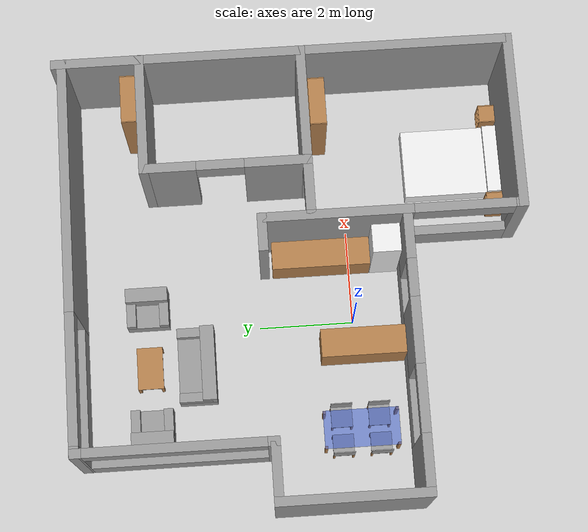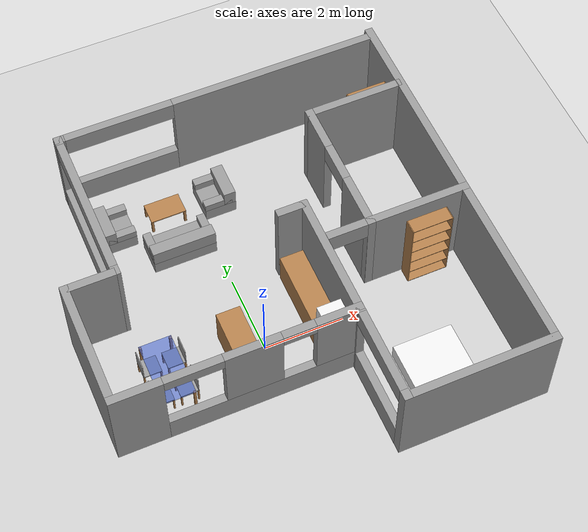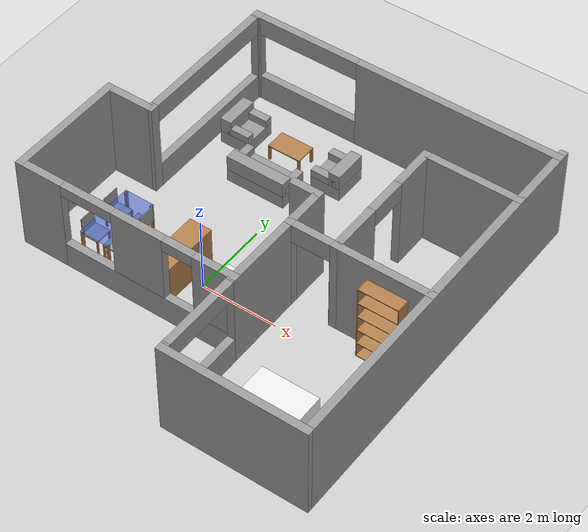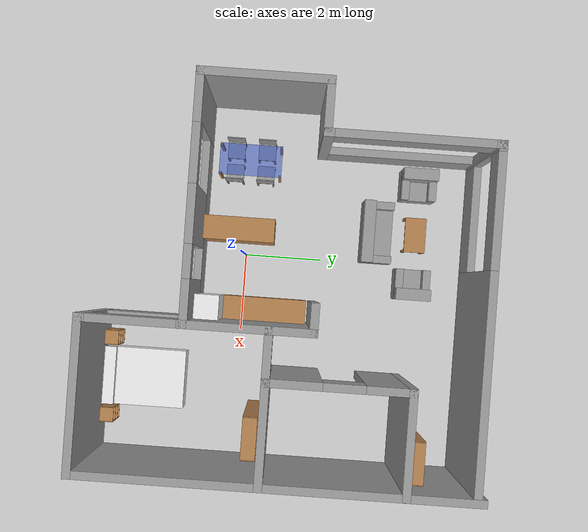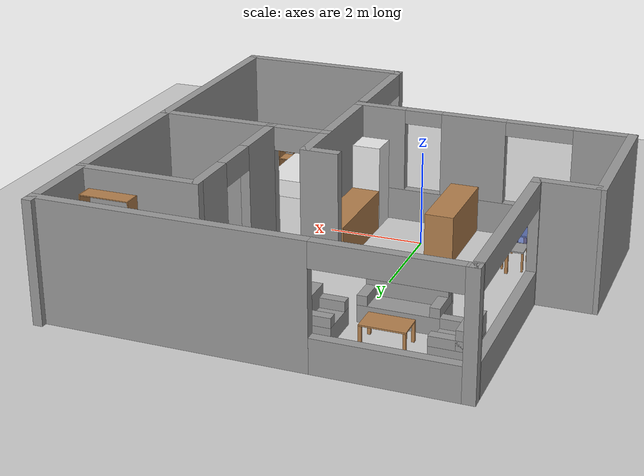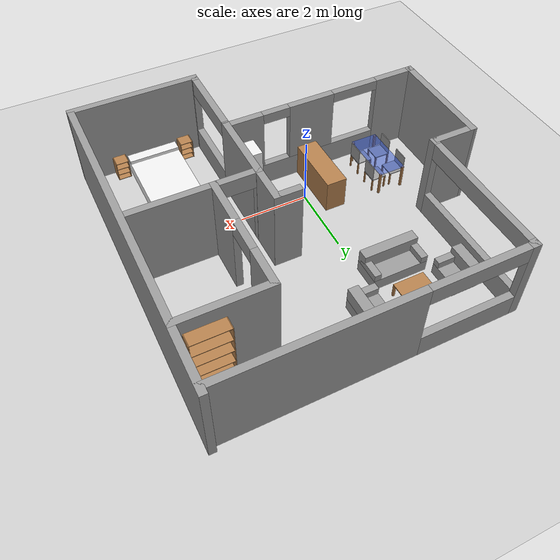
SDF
<sdf version="1.4">
 <world name="GrannyAnnie">
  <include><uri>model://house_int2</uri></include>
  <include><uri>model://ground_plane</uri></include>
  <light name="sun" type="directional">
   <pose>0 0 10 0 -0 0</pose>
   <diffuse>0.8 0.8 0.8 1</diffuse>
   <specular>0.2 0.2 0.2 1</specular>
   <attenuation>
    <range>1000</range>
    <constant>0.9</constant>
    <linear>0.01</linear>
    <quadratic>0.001</quadratic>
   </attenuation>
   <direction>-0.5 0.1 -0.9</direction>
  </light>
  <scene><ambient>0.4 0.4 0.4 1</ambient><background>0.7 0.7 0.7 1</background><shadows>1</shadows></scene>
 </world>
</sdf>

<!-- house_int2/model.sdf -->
<sdf version='1.4'>
  <model name='house_int2'>
    <model name='mesa_comedor'>
      <static>true</static>
      <link name='mesa_link'>
        <pose>0 0 0 0 -0 0</pose>
        <inertial>
          <pose>1.58603e-17 0 0.513571 0 -0 0</pose>
          <mass>70</mass>
          <inertia>
            <ixx>1.28229</ixx>
            <ixy>0</ixy>
            <ixz>5.70179e-17</ixz>
            <iyy>3.10629</iyy>
            <iyz>0</iyz>
            <izz>3.4192</izz>
          </inertia>
        </inertial>
        <collision name='mesa_link_collision'>
          <pose>0 0 0.725 0 -0 0</pose>
          <geometry>
            <box>
              <size>1.6 0.8 0.03</size>
            </box>
          </geometry>
          <surface>
            <contact>
              <ode/>
            </contact>
            <friction>
              <ode>
                <mu>1</mu>
                <mu2>1</mu2>
              </ode>
            </friction>
            <bounce/>
          </surface>
          <max_contacts>10</max_contacts>
        </collision>
        <collision name='mesa_link_collision_pata_1_link'>
          <pose>0.77 0.37 0.355 0 -0 0</pose>
          <geometry>
            <box>
              <size>0.06 0.06 0.71</size>
            </box>
          </geometry>
          <surface>
            <contact>
              <ode/>
            </contact>
            <friction>
              <ode>
                <mu>1</mu>
                <mu2>1</mu2>
              </ode>
            </friction>
            <bounce/>
          </surface>
          <surface>
            <contact>
              <ode/>
            </contact>
            <friction>
              <ode>
                <mu>1</mu>
                <mu2>1</mu2>
              </ode>
            </friction>
          </surface>
          <max_contacts>10</max_contacts>
        </collision>
        <collision name='mesa_link_collision_pata_2_link'>
          <pose>0.77 -0.37 0.355 0 -0 0</pose>
          <geometry>
            <box>
              <size>0.06 0.06 0.71</size>
            </box>
          </geometry>
          <surface>
            <contact>
              <ode/>
            </contact>
            <friction>
              <ode>
                <mu>1</mu>
                <mu2>1</mu2>
              </ode>
            </friction>
            <bounce/>
          </surface>
          <surface>
            <contact>
              <ode/>
            </contact>
            <friction>
              <ode>
                <mu>1</mu>
                <mu2>1</mu2>
              </ode>
            </friction>
          </surface>
          <max_contacts>10</max_contacts>
        </collision>
        <collision name='mesa_link_collision_pata_3_link'>
          <pose>-0.77 -0.37 0.355 0 -0 0</pose>
          <geometry>
            <box>
              <size>0.06 0.06 0.71</size>
            </box>
          </geometry>
          <surface>
            <contact>
              <ode/>
            </contact>
            <friction>
              <ode>
                <mu>1</mu>
                <mu2>1</mu2>
              </ode>
            </friction>
            <bounce/>
          </surface>
          <surface>
            <contact>
              <ode/>
            </contact>
            <friction>
              <ode>
                <mu>1</mu>
                <mu2>1</mu2>
              </ode>
            </friction>
          </surface>
          <max_contacts>10</max_contacts>
        </collision>
        <collision name='mesa_link_collision_pata_4_link'>
          <pose>-0.77 0.37 0.355 0 -0 0</pose>
          <geometry>
            <box>
              <size>0.06 0.06 0.71</size>
            </box>
          </geometry>
          <surface>
            <contact>
              <ode/>
            </contact>
            <friction>
              <ode>
                <mu>1</mu>
                <mu2>1</mu2>
              </ode>
            </friction>
            <bounce/>
          </surface>
          <surface>
            <contact>
              <ode/>
            </contact>
            <friction>
              <ode>
                <mu>1</mu>
                <mu2>1</mu2>
              </ode>
            </friction>
          </surface>
          <max_contacts>10</max_contacts>
        </collision>
        <visual name='mesa_link_visual'>
          <pose>0 0 0.725 0 -0 0</pose>
          <geometry>
            <box>
              <size>1.6 0.8 0.03</size>
            </box>
          </geometry>
          <material>
            <script>
              <name>Gazebo/BlueTransparent</name>
              <uri>__default__</uri>
            </script>
          </material>
        </visual>
        <visual name='mesa_link_visual_pata_1_link'>
          <pose>0.77 0.37 0.355 0 -0 0</pose>
          <geometry>
            <box>
              <size>0.06 0.06 0.71</size>
            </box>
          </geometry>
          <material>
            <script>
              <name>Gazebo/Wood</name>
              <uri>__default__</uri>
            </script>
          </material>
        </visual>
        <visual name='mesa_link_visual_pata_2_link'>
          <pose>0.77 -0.37 0.355 0 -0 0</pose>
          <geometry>
            <box>
              <size>0.06 0.06 0.71</size>
            </box>
          </geometry>
          <material>
            <script>
              <name>Gazebo/Wood</name>
              <uri>__default__</uri>
            </script>
          </material>
        </visual>
        <visual name='mesa_link_visual_pata_3_link'>
          <pose>-0.77 -0.37 0.355 0 -0 0</pose>
          <geometry>
            <box>
              <size>0.06 0.06 0.71</size>
            </box>
          </geometry>
          <material>
            <script>
              <name>Gazebo/Wood</name>
              <uri>__default__</uri>
            </script>
          </material>
        </visual>
        <visual name='mesa_link_visual_pata_4_link'>
          <pose>-0.77 0.37 0.355 0 -0 0</pose>
          <geometry>
            <box>
              <size>0.06 0.06 0.71</size>
            </box>
          </geometry>
          <material>
            <script>
              <name>Gazebo/Wood</name>
              <uri>__default__</uri>
            </script>
          </material>
        </visual>
        <velocity_decay>
          <linear>0</linear>
          <angular>0</angular>
        </velocity_decay>
        <velocity_decay>
          <linear>0</linear>
          <angular>0</angular>
        </velocity_decay>
        <velocity_decay>
          <linear>0</linear>
          <angular>0</angular>
        </velocity_decay>
        <velocity_decay>
          <linear>0</linear>
          <angular>0</angular>
        </velocity_decay>
        <gravity>1</gravity>
        <velocity_decay>
          <linear>0</linear>
          <angular>0</angular>
        </velocity_decay>
        <self_collide>1</self_collide>
        <kinematic>0</kinematic>
      </link>
      <pose>-2.4 0 0 0 -0 1.57</pose>
      <static>0</static>
    </model>

    <model name='RoCKIn@Home'>
      <static>true</static>
      <link name='Wall_12'>
        <collision name='Wall_12_Collision'>
          <geometry>
            <box>
              <size>2.6 0.2 2.5</size>
            </box>
          </geometry>
          <pose>0 0 1.25 0 -0 0</pose>
          <max_contacts>10</max_contacts>
          <surface>
            <bounce/>
            <friction>
              <ode/>
            </friction>
            <contact>
              <ode/>
            </contact>
          </surface>
        </collision>
        <visual name='Wall_12_Visual'>
          <pose>0 0 1.25 0 -0 0</pose>
          <geometry>
            <box>
              <size>2.6 0.2 2.5</size>
            </box>
          </geometry>
          <material>
            <script>
              <uri>file://media/materials/scripts/gazebo.material</uri>
              <name>Gazebo/Grey</name>
            </script>
          </material>
        </visual>
        <velocity_decay>
          <linear>0</linear>
          <angular>0</angular>
        </velocity_decay>
        <pose>7.8 1.205 0 0 -0 1.5708</pose>
        <self_collide>0</self_collide>
        <kinematic>0</kinematic>
        <gravity>1</gravity>
      </link>
      <link name='Wall_14'>
        <pose>6.0996 2.4048 0 0 -0 3.14159</pose>
        <visual name='Wall_14_Visual_0'>
          <pose>-1.20789 0 1.25 0 -0 0</pose>
          <geometry>
            <box>
              <size>1.18422 0.2 2.5</size>
            </box>
          </geometry>
          <material>
            <script>
              <uri>file://media/materials/scripts/gazebo.material</uri>
              <name>Gazebo/Grey</name>
            </script>
          </material>
        </visual>
        <collision name='Wall_14_Collision_0'>
          <geometry>
            <box>
              <size>1.18422 0.2 2.5</size>
            </box>
          </geometry>
          <pose>-1.20789 0 1.25 0 -0 0</pose>
          <max_contacts>10</max_contacts>
          <surface>
            <bounce/>
            <friction>
              <ode/>
            </friction>
            <contact>
              <ode/>
            </contact>
          </surface>
        </collision>
        <visual name='Wall_14_Visual_1'>
          <pose>1.09211 0 1.25 0 -0 0</pose>
          <geometry>
            <box>
              <size>1.41579 0.2 2.5</size>
            </box>
          </geometry>
          <material>
            <script>
              <uri>file://media/materials/scripts/gazebo.material</uri>
              <name>Gazebo/Grey</name>
            </script>
          </material>
        </visual>
        <collision name='Wall_14_Collision_1'>
          <geometry>
            <box>
              <size>1.41579 0.2 2.5</size>
            </box>
          </geometry>
          <pose>1.09211 0 1.25 0 -0 0</pose>
          <max_contacts>10</max_contacts>
          <surface>
            <bounce/>
            <friction>
              <ode/>
            </friction>
            <contact>
              <ode/>
            </contact>
          </surface>
        </collision>
        <visual name='Wall_14_Visual_2'>
          <pose>-0.115785 0 2.25 0 -0 0</pose>
          <geometry>
            <box>
              <size>1 0.2 0.5</size>
            </box>
          </geometry>
          <material>
            <script>
              <uri>file://media/materials/scripts/gazebo.material</uri>
              <name>Gazebo/Grey</name>
            </script>
          </material>
        </visual>
        <collision name='Wall_14_Collision_2'>
          <geometry>
            <box>
              <size>1 0.2 0.5</size>
            </box>
          </geometry>
          <pose>-0.115785 0 2.25 0 -0 0</pose>
          <max_contacts>10</max_contacts>
          <surface>
            <bounce/>
            <friction>
              <ode/>
            </friction>
            <contact>
              <ode/>
            </contact>
          </surface>
        </collision>
        <velocity_decay>
          <linear>0</linear>
          <angular>0</angular>
        </velocity_decay>
        <self_collide>0</self_collide>
        <kinematic>0</kinematic>
        <gravity>1</gravity>
      </link>
      <link name='Wall_16'>
        <collision name='Wall_16_Collision'>
          <geometry>
            <box>
              <size>2.60492 0.2 2.5</size>
            </box>
          </geometry>
          <pose>0 0 1.25 0 -0 0</pose>
          <max_contacts>10</max_contacts>
          <surface>
            <bounce/>
            <friction>
              <ode/>
            </friction>
            <contact>
              <ode/>
            </contact>
          </surface>
        </collision>
        <visual name='Wall_16_Visual'>
          <pose>0 0 1.25 0 -0 0</pose>
          <geometry>
            <box>
              <size>2.60492 0.2 2.5</size>
            </box>
          </geometry>
          <material>
            <script>
              <uri>file://media/materials/scripts/gazebo.material</uri>
              <name>Gazebo/Grey</name>
            </script>
          </material>
        </visual>
        <velocity_decay>
          <linear>0</linear>
          <angular>0</angular>
        </velocity_decay>
        <pose>4.39903 1.20277 0 0 -0 1.5708</pose>
        <self_collide>0</self_collide>
        <kinematic>0</kinematic>
        <gravity>1</gravity>
      </link>
      <link name='Wall_18'>
        <collision name='Wall_18_Collision'>
          <geometry>
            <box>
              <size>3.8 0.2 2.5</size>
            </box>
          </geometry>
          <pose>0 0 1.25 0 -0 0</pose>
          <max_contacts>10</max_contacts>
          <surface>
            <bounce/>
            <friction>
              <ode/>
            </friction>
            <contact>
              <ode/>
            </contact>
          </surface>
        </collision>
        <visual name='Wall_18_Visual'>
          <pose>0 0 1.25 0 -0 0</pose>
          <geometry>
            <box>
              <size>3.8 0.2 2.5</size>
            </box>
          </geometry>
          <material>
            <script>
              <uri>file://media/materials/scripts/gazebo.material</uri>
              <name>Gazebo/Grey</name>
            </script>
          </material>
        </visual>
        <velocity_decay>
          <linear>0</linear>
          <angular>0</angular>
        </velocity_decay>
        <pose>0.024876 1.80003 0 0 -0 1.5708</pose>
        <self_collide>0</self_collide>
        <kinematic>0</kinematic>
        <gravity>1</gravity>
      </link>
      <link name='Wall_2'>
        <pose>5.50266 0 0 0 -0 0</pose>
        <visual name='Wall_2_Visual_0'>
          <pose>-0.649274 0 1.25 0 -0 0</pose>
          <geometry>
            <box>
              <size>9.599997 0.2 2.5</size>
            </box>
          </geometry>
          <material>
            <script>
              <uri>file://media/materials/scripts/gazebo.material</uri>
              <name>Gazebo/Grey</name>
            </script>
          </material>
        </visual>
        <collision name='Wall_2_Collision_0'>
          <geometry>
            <box>
              <size>9.599997 0.2 2.5</size>
            </box>
          </geometry>
          <pose>-0.649274 0 1.25 0 -0 0</pose>
          <max_contacts>10</max_contacts>
          <surface>
            <bounce/>
            <friction>
              <ode/>
            </friction>
            <contact>
              <ode/>
            </contact>
          </surface>
        </collision>
        <velocity_decay>
          <linear>0</linear>
          <angular>0</angular>
        </velocity_decay>
        <self_collide>0</self_collide>
        <kinematic>0</kinematic>
        <gravity>1</gravity>
      </link>
      <link name='Wall_20'>
        <pose>2.72456 3.60059 0 0 -0 0</pose>
        <visual name='Wall_20_Visual_0'>
          <pose>-2.67396 0 1.25 0 -0 0</pose>
          <geometry>
            <box>
              <size>0.251208 0.2 2.5</size>
            </box>
          </geometry>
          <material>
            <script>
              <uri>file://media/materials/scripts/gazebo.material</uri>
              <name>Gazebo/Grey</name>
            </script>
          </material>
        </visual>
        <collision name='Wall_20_Collision_0'>
          <geometry>
            <box>
              <size>0.251208 0.2 2.5</size>
            </box>
          </geometry>
          <pose>-2.67396 0 1.25 0 -0 0</pose>
          <max_contacts>10</max_contacts>
          <surface>
            <bounce/>
            <friction>
              <ode/>
            </friction>
            <contact>
              <ode/>
            </contact>
          </surface>
        </collision>
        <visual name='Wall_20_Visual_1'>
          <pose>1.1766 0 1.25 0 -0 0</pose>
          <geometry>
            <box>
              <size>3.24591 0.2 2.5</size>
            </box>
          </geometry>
          <material>
            <script>
              <uri>file://media/materials/scripts/gazebo.material</uri>
              <name>Gazebo/Grey</name>
            </script>
          </material>
        </visual>
        <collision name='Wall_20_Collision_1'>
          <geometry>
            <box>
              <size>3.24591 0.2 2.5</size>
            </box>
          </geometry>
          <pose>1.1766 0 1.25 0 -0 0</pose>
          <max_contacts>10</max_contacts>
          <surface>
            <bounce/>
            <friction>
              <ode/>
            </friction>
            <contact>
              <ode/>
            </contact>
          </surface>
        </collision>
        <visual name='Wall_20_Visual_2'>
          <pose>-1.49735 0 2.25 0 -0 0</pose>
          <geometry>
            <box>
              <size>2.102 0.2 0.5</size>
            </box>
          </geometry>
          <material>
            <script>
              <uri>file://media/materials/scripts/gazebo.material</uri>
              <name>Gazebo/Grey</name>
            </script>
          </material>
        </visual>
        <collision name='Wall_20_Collision_2'>
          <geometry>
            <box>
              <size>2.102 0.2 0.5</size>
            </box>
          </geometry>
          <pose>-1.49735 0 2.25 0 -0 0</pose>
          <max_contacts>10</max_contacts>
          <surface>
            <bounce/>
            <friction>
              <ode/>
            </friction>
            <contact>
              <ode/>
            </contact>
          </surface>
        </collision>
        <visual name='Wall_20_Visual_3'>
          <pose>-1.49735 0 0.35 0 -0 0</pose>
          <geometry>
            <box>
              <size>2.102 0.2 0.7</size>
            </box>
          </geometry>
          <material>
            <script>
              <uri>file://media/materials/scripts/gazebo.material</uri>
              <name>Gazebo/Grey</name>
            </script>
          </material>
        </visual>
        <collision name='Wall_20_Collision_3'>
          <geometry>
            <box>
              <size>2.102 0.2 0.7</size>
            </box>
          </geometry>
          <pose>-1.49735 0 0.35 0 -0 0</pose>
          <max_contacts>10</max_contacts>
          <surface>
            <bounce/>
            <friction>
              <ode/>
            </friction>
            <contact>
              <ode/>
            </contact>
          </surface>
        </collision>
        <velocity_decay>
          <linear>0</linear>
          <angular>0</angular>
        </velocity_decay>
        <self_collide>0</self_collide>
        <kinematic>0</kinematic>
        <gravity>1</gravity>
      </link>
      <link name='Wall_22'>
        <pose>4.39856 3.00206 0 0 -0 1.5708</pose>
        <visual name='Wall_22_Visual_0'>
          <pose>-0.601085 0 1.25 0 -0 0</pose>
          <geometry>
            <box>
              <size>0.194709 0.2 2.5</size>
            </box>
          </geometry>
          <material>
            <script>
              <uri>file://media/materials/scripts/gazebo.material</uri>
              <name>Gazebo/Grey</name>
            </script>
          </material>
        </visual>
        <collision name='Wall_22_Collision_0'>
          <geometry>
            <box>
              <size>0.194709 0.2 2.5</size>
            </box>
          </geometry>
          <pose>-0.601085 0 1.25 0 -0 0</pose>
          <max_contacts>10</max_contacts>
          <surface>
            <bounce/>
            <friction>
              <ode/>
            </friction>
            <contact>
              <ode/>
            </contact>
          </surface>
        </collision>
        <visual name='Wall_22_Visual_1'>
          <pose>0.597355 0 1.25 0 -0 0</pose>
          <geometry>
            <box>
              <size>0.202171 0.2 2.5</size>
            </box>
          </geometry>
          <material>
            <script>
              <uri>file://media/materials/scripts/gazebo.material</uri>
              <name>Gazebo/Grey</name>
            </script>
          </material>
        </visual>
        <collision name='Wall_22_Collision_1'>
          <geometry>
            <box>
              <size>0.202171 0.2 2.5</size>
            </box>
          </geometry>
          <pose>0.597355 0 1.25 0 -0 0</pose>
          <max_contacts>10</max_contacts>
          <surface>
            <bounce/>
            <friction>
              <ode/>
            </friction>
            <contact>
              <ode/>
            </contact>
          </surface>
        </collision>
        <visual name='Wall_22_Visual_2'>
          <pose>-0.003731 0 2.25 0 -0 0</pose>
          <geometry>
            <box>
              <size>1 0.2 0.5</size>
            </box>
          </geometry>
          <material>
            <script>
              <uri>file://media/materials/scripts/gazebo.material</uri>
              <name>Gazebo/Grey</name>
            </script>
          </material>
        </visual>
        <collision name='Wall_22_Collision_2'>
          <geometry>
            <box>
              <size>1 0.2 0.5</size>
            </box>
          </geometry>
          <pose>-0.003731 0 2.25 0 -0 0</pose>
          <max_contacts>10</max_contacts>
          <surface>
            <bounce/>
            <friction>
              <ode/>
            </friction>
            <contact>
              <ode/>
            </contact>
          </surface>
        </collision>
        <velocity_decay>
          <linear>0</linear>
          <angular>0</angular>
        </velocity_decay>
        <self_collide>0</self_collide>
        <kinematic>0</kinematic>
        <gravity>1</gravity>
      </link>
      <link name='Wall_24'>
        <pose>7.42703 8.20242 0 0 -0 3.14159</pose>
        <visual name='Wall_24_Visual_0'>
          <pose>-1.97924 0 1.25 0 -0 0</pose>
          <geometry>
            <box>
              <size>0.241529 0.2 2.5</size>
            </box>
          </geometry>
          <material>
            <script>
              <uri>file://media/materials/scripts/gazebo.material</uri>
              <name>Gazebo/Grey</name>
            </script>
          </material>
        </visual>
        <collision name='Wall_24_Collision_0'>
          <geometry>
            <box>
              <size>0.241529 0.2 2.5</size>
            </box>
          </geometry>
          <pose>-1.97924 0 1.25 0 -0 0</pose>
          <max_contacts>10</max_contacts>
          <surface>
            <bounce/>
            <friction>
              <ode/>
            </friction>
            <contact>
              <ode/>
            </contact>
          </surface>
        </collision>
        <visual name='Wall_24_Visual_1'>
          <pose>1.97395 0 1.25 0 -0 0</pose>
          <geometry>
            <box>
              <size>0.252091 0.2 2.5</size>
            </box>
          </geometry>
          <material>
            <script>
              <uri>file://media/materials/scripts/gazebo.material</uri>
              <name>Gazebo/Grey</name>
            </script>
          </material>
        </visual>
        <collision name='Wall_24_Collision_1'>
          <geometry>
            <box>
              <size>0.252091 0.2 2.5</size>
            </box>
          </geometry>
          <pose>1.97395 0 1.25 0 -0 0</pose>
          <max_contacts>10</max_contacts>
          <surface>
            <bounce/>
            <friction>
              <ode/>
            </friction>
            <contact>
              <ode/>
            </contact>
          </surface>
        </collision>
        <visual name='Wall_24_Visual_2'>
          <pose>-0.005281 0 2.25 0 -0 0</pose>
          <geometry>
            <box>
              <size>3.70638 0.2 0.5</size>
            </box>
          </geometry>
          <material>
            <script>
              <uri>file://media/materials/scripts/gazebo.material</uri>
              <name>Gazebo/Grey</name>
            </script>
          </material>
        </visual>
        <collision name='Wall_24_Collision_2'>
          <geometry>
            <box>
              <size>3.70638 0.2 0.5</size>
            </box>
          </geometry>
          <pose>-0.005281 0 2.25 0 -0 0</pose>
          <max_contacts>10</max_contacts>
          <surface>
            <bounce/>
            <friction>
              <ode/>
            </friction>
            <contact>
              <ode/>
            </contact>
          </surface>
        </collision>
        <visual name='Wall_24_Visual_3'>
          <pose>-0.005281 0 0.35 0 -0 0</pose>
          <geometry>
            <box>
              <size>3.70638 0.2 0.7</size>
            </box>
          </geometry>
          <material>
            <script>
              <uri>file://media/materials/scripts/gazebo.material</uri>
              <name>Gazebo/Grey</name>
            </script>
          </material>
        </visual>
        <collision name='Wall_24_Collision_3'>
          <geometry>
            <box>
              <size>3.70638 0.2 0.7</size>
            </box>
          </geometry>
          <pose>-0.005281 0 0.35 0 -0 0</pose>
          <max_contacts>10</max_contacts>
          <surface>
            <bounce/>
            <friction>
              <ode/>
            </friction>
            <contact>
              <ode/>
            </contact>
          </surface>
        </collision>
        <velocity_decay>
          <linear>0</linear>
          <angular>0</angular>
        </velocity_decay>
        <self_collide>0</self_collide>
        <kinematic>0</kinematic>
        <gravity>1</gravity>
      </link>
      <link name='Wall_28'>
        <collision name='Wall_28_Collision'>
          <geometry>
            <box>
              <size>3.2 0.2 2.5</size>
            </box>
          </geometry>
          <pose>0 0 1.25 0 -0 0</pose>
          <max_contacts>10</max_contacts>
          <surface>
            <bounce/>
            <friction>
              <ode/>
            </friction>
            <contact>
              <ode/>
            </contact>
          </surface>
        </collision>
        <visual name='Wall_28_Visual'>
          <pose>0 0 1.25 0 -0 0</pose>
          <geometry>
            <box>
              <size>3.2 0.2 2.5</size>
            </box>
          </geometry>
          <material>
            <script>
              <uri>file://media/materials/scripts/gazebo.material</uri>
              <name>Gazebo/Grey</name>
            </script>
          </material>
        </visual>
        <velocity_decay>
          <linear>0</linear>
          <angular>0</angular>
        </velocity_decay>
        <pose>3.92571 9.40229 0 0 -0 3.14159</pose>
        <self_collide>0</self_collide>
        <kinematic>0</kinematic>
        <gravity>1</gravity>
      </link>
      <link name='Wall_30'>
        <pose>2.42541 6.50159 0 0 0 -1.5708</pose>
        <visual name='Wall_30_Visual_0'>
          <pose>-2.363 0 1.25 0 -0 0</pose>
          <geometry>
            <box>
              <size>1.27269 0.2 2.5</size>
            </box>
          </geometry>
          <material>
            <script>
              <uri>file://media/materials/scripts/gazebo.material</uri>
              <name>Gazebo/Grey</name>
            </script>
          </material>
        </visual>
        <collision name='Wall_30_Collision_0'>
          <geometry>
            <box>
              <size>1.27269 0.2 2.5</size>
            </box>
          </geometry>
          <pose>-2.363 0 1.25 0 -0 0</pose>
          <max_contacts>10</max_contacts>
          <surface>
            <bounce/>
            <friction>
              <ode/>
            </friction>
            <contact>
              <ode/>
            </contact>
          </surface>
        </collision>
        <visual name='Wall_30_Visual_1'>
          <pose>0.636346 0 0.35 0 -0 0</pose>
          <geometry>
            <box>
              <size>4.726 0.2 0.7</size>
            </box>
          </geometry>
          <material>
            <script>
              <uri>file://media/materials/scripts/gazebo.material</uri>
              <name>Gazebo/Grey</name>
            </script>
          </material>
        </visual>
        <collision name='Wall_30_Collision_1'>
          <geometry>
            <box>
              <size>4.726 0.2 0.7</size>
            </box>
          </geometry>
          <pose>0.636346 0 0.35 0 -0 0</pose>
          <max_contacts>10</max_contacts>
          <surface>
            <bounce/>
            <friction>
              <ode/>
            </friction>
            <contact>
              <ode/>
            </contact>
          </surface>
        </collision>
        <visual name='Wall_30_Visual_2'>
          <pose>0.36359 0 1.6 0 -0 0</pose>
          <geometry>
            <box>
              <size>1.38049 0.2 1.8</size>
            </box>
          </geometry>
          <material>
            <script>
              <uri>file://media/materials/scripts/gazebo.material</uri>
              <name>Gazebo/Grey</name>
            </script>
          </material>
        </visual>
        <collision name='Wall_30_Collision_2'>
          <geometry>
            <box>
              <size>1.38049 0.2 1.8</size>
            </box>
          </geometry>
          <pose>0.36359 0 1.6 0 -0 0</pose>
          <max_contacts>10</max_contacts>
          <surface>
            <bounce/>
            <friction>
              <ode/>
            </friction>
            <contact>
              <ode/>
            </contact>
          </surface>
        </collision>
        <visual name='Wall_30_Visual_3'>
          <pose>2.42659 0 1.6 0 -0 0</pose>
          <geometry>
            <box>
              <size>1.14551 0.2 1.8</size>
            </box>
          </geometry>
          <material>
            <script>
              <uri>file://media/materials/scripts/gazebo.material</uri>
              <name>Gazebo/Grey</name>
            </script>
          </material>
        </visual>
        <collision name='Wall_30_Collision_3'>
          <geometry>
            <box>
              <size>1.14551 0.2 1.8</size>
            </box>
          </geometry>
          <pose>2.42659 0 1.6 0 -0 0</pose>
          <max_contacts>10</max_contacts>
          <surface>
            <bounce/>
            <friction>
              <ode/>
            </friction>
            <contact>
              <ode/>
            </contact>
          </surface>
        </collision>
        <visual name='Wall_30_Visual_4'>
          <pose>-1.02665 0 2.35 0 -0 0</pose>
          <geometry>
            <box>
              <size>1.4 0.2 0.3</size>
            </box>
          </geometry>
          <material>
            <script>
              <uri>file://media/materials/scripts/gazebo.material</uri>
              <name>Gazebo/Grey</name>
            </script>
          </material>
        </visual>
        <collision name='Wall_30_Collision_4'>
          <geometry>
            <box>
              <size>1.4 0.2 0.3</size>
            </box>
          </geometry>
          <pose>-1.02665 0 2.35 0 -0 0</pose>
          <max_contacts>10</max_contacts>
          <surface>
            <bounce/>
            <friction>
              <ode/>
            </friction>
            <contact>
              <ode/>
            </contact>
          </surface>
        </collision>
        <visual name='Wall_30_Visual_5'>
          <pose>1.45383 0 2.35 0 -0 0</pose>
          <geometry>
            <box>
              <size>0.8 0.2 0.3</size>
            </box>
          </geometry>
          <material>
            <script>
              <uri>file://media/materials/scripts/gazebo.material</uri>
              <name>Gazebo/Grey</name>
            </script>
          </material>
        </visual>
        <collision name='Wall_30_Collision_5'>
          <geometry>
            <box>
              <size>0.8 0.2 0.3</size>
            </box>
          </geometry>
          <pose>1.45383 0 2.35 0 -0 0</pose>
          <max_contacts>10</max_contacts>
          <surface>
            <bounce/>
            <friction>
              <ode/>
            </friction>
            <contact>
              <ode/>
            </contact>
          </surface>
        </collision>
        <velocity_decay>
          <linear>0</linear>
          <angular>0</angular>
        </velocity_decay>
        <self_collide>0</self_collide>
        <kinematic>0</kinematic>
        <gravity>1</gravity>
      </link>
      <link name='Wall_32'>
        <pose>5.42654 8.80216 0 0 0 -1.5708</pose>
        <visual name='Wall_32_Visual_0'>
          <pose>0 0 1.25 0 -0 0</pose>
          <geometry>
            <box>
              <size>1.20 0.2 2.5</size>
            </box>
          </geometry>
          <material>
            <script>
              <uri>file://media/materials/scripts/gazebo.material</uri>
              <name>Gazebo/Grey</name>
            </script>
          </material>
        </visual>
        <collision name='Wall_32_Collision_0'>
          <geometry>
            <box>
              <size>1.20 0.2 2.5</size>
            </box>
          </geometry>
          <pose>0 0 1.25 0 -0 0</pose>
          <max_contacts>10</max_contacts>
          <surface>
            <bounce/>
            <friction>
              <ode/>
            </friction>
            <contact>
              <ode/>
            </contact>
          </surface>
        </collision>
      </link>
      <link name='Wall_35'>
        <collision name='Wall_35_Collision'>
          <geometry>
            <box>
              <size>0.8 0.2 2.5</size>
            </box>
          </geometry>
          <pose>0 0 1.25 0 -0 0</pose>
          <max_contacts>10</max_contacts>
          <surface>
            <bounce/>
            <friction>
              <ode/>
            </friction>
            <contact>
              <ode/>
            </contact>
          </surface>
        </collision>
        <visual name='Wall_35_Visual'>
          <pose>0 0 1.25 0 -0 0</pose>
          <geometry>
            <box>
              <size>0.8 0.2 2.5</size>
            </box>
          </geometry>
          <material>
            <script>
              <uri>file://media/materials/scripts/gazebo.material</uri>
              <name>Gazebo/Grey</name>
            </script>
          </material>
        </visual>
        <velocity_decay>
          <linear>0</linear>
          <angular>0</angular>
        </velocity_decay>
        <pose>5.42451 3.90082 0 0 -0 1.5708</pose>
        <self_collide>0</self_collide>
        <kinematic>0</kinematic>
        <gravity>1</gravity>
      </link>
      <link name='Wall_8'>
        <pose>9.42875 4.1026 0 0 -0 1.5708</pose>
        <visual name='Wall_8_Visual_0'>
          <pose>-1.48935 0 1.25 0 -0 0</pose>
          <geometry>
            <box>
              <size>5.42201 0.2 2.5</size>
            </box>
          </geometry>
          <material>
            <script>
              <uri>file://media/materials/scripts/gazebo.material</uri>
              <name>Gazebo/Grey</name>
            </script>
          </material>
        </visual>
        <collision name='Wall_8_Collision_0'>
          <geometry>
            <box>
              <size>5.42201 0.2 2.5</size>
            </box>
          </geometry>
          <pose>-1.48935 0 1.25 0 -0 0</pose>
          <max_contacts>10</max_contacts>
          <surface>
            <bounce/>
            <friction>
              <ode/>
            </friction>
            <contact>
              <ode/>
            </contact>
          </surface>
        </collision>
        <visual name='Wall_8_Visual_1'>
          <pose>4.07465 0 1.25 0 -0 0</pose>
          <geometry>
            <box>
              <size>0.251416 0.2 2.5</size>
            </box>
          </geometry>
          <material>
            <script>
              <uri>file://media/materials/scripts/gazebo.material</uri>
              <name>Gazebo/Grey</name>
            </script>
          </material>
        </visual>
        <collision name='Wall_8_Collision_1'>
          <geometry>
            <box>
              <size>0.251416 0.2 2.5</size>
            </box>
          </geometry>
          <pose>4.07465 0 1.25 0 -0 0</pose>
          <max_contacts>10</max_contacts>
          <surface>
            <bounce/>
            <friction>
              <ode/>
            </friction>
            <contact>
              <ode/>
            </contact>
          </surface>
        </collision>
        <visual name='Wall_8_Visual_2'>
          <pose>2.5853 0 2.25 0 -0 0</pose>
          <geometry>
            <box>
              <size>2.72728 0.2 0.5</size>
            </box>
          </geometry>
          <material>
            <script>
              <uri>file://media/materials/scripts/gazebo.material</uri>
              <name>Gazebo/Grey</name>
            </script>
          </material>
        </visual>
        <collision name='Wall_8_Collision_2'>
          <geometry>
            <box>
              <size>2.72728 0.2 0.5</size>
            </box>
          </geometry>
          <pose>2.5853 0 2.25 0 -0 0</pose>
          <max_contacts>10</max_contacts>
          <surface>
            <bounce/>
            <friction>
              <ode/>
            </friction>
            <contact>
              <ode/>
            </contact>
          </surface>
        </collision>
        <visual name='Wall_8_Visual_3'>
          <pose>2.5853 0 0.35 0 -0 0</pose>
          <geometry>
            <box>
              <size>2.72728 0.2 0.7</size>
            </box>
          </geometry>
          <material>
            <script>
              <uri>file://media/materials/scripts/gazebo.material</uri>
              <name>Gazebo/Grey</name>
            </script>
          </material>
        </visual>
        <collision name='Wall_8_Collision_3'>
          <geometry>
            <box>
              <size>2.72728 0.2 0.7</size>
            </box>
          </geometry>
          <pose>2.5853 0 0.35 0 -0 0</pose>
          <max_contacts>10</max_contacts>
          <surface>
            <bounce/>
            <friction>
              <ode/>
            </friction>
            <contact>
              <ode/>
            </contact>
          </surface>
        </collision>
        <velocity_decay>
          <linear>0</linear>
          <angular>0</angular>
        </velocity_decay>
        <self_collide>0</self_collide>
        <kinematic>0</kinematic>
        <gravity>1</gravity>
      </link>
      <static>1</static>
      <pose>5.4 -3.6 0 0 -0 1.57</pose>
    </model>
    <model name='silla_1'>
      <static>true</static>
      <link name='silla_link'>
        <pose>0 0 0 0 -0 0</pose>
        <inertial>
          <pose>0.0215 0 0.353 0 -0 0</pose>
          <mass>20</mass>
          <inertia>
            <ixx>0.674432</ixx>
            <ixy>0</ixy>
            <ixz>-0.012986</ixz>
            <iyy>0.682753</iyy>
            <iyz>0</iyz>
            <izz>0.675561</izz>
          </inertia>
        </inertial>
        <collision name='silla_link_collision'>
          <pose>0 0 0.415 0 -0 0</pose>
          <geometry>
            <box>
              <size>0.45 0.45 0.03</size>
            </box>
          </geometry>
          <surface>
            <contact>
              <ode/>
            </contact>
            <friction>
              <ode>
                <mu>1</mu>
                <mu2>1</mu2>
              </ode>
            </friction>
            <bounce/>
          </surface>
          <max_contacts>10</max_contacts>
        </collision>
        <collision name='silla_link_collision_pata_1_link'>
          <pose>0.205 0.205 0.2 0 -0 0</pose>
          <geometry>
            <box>
              <size>0.04 0.04 0.4</size>
            </box>
          </geometry>
          <surface>
            <contact>
              <ode/>
            </contact>
            <friction>
              <ode>
                <mu>1</mu>
                <mu2>1</mu2>
              </ode>
            </friction>
            <bounce/>
          </surface>
          <surface>
            <contact>
              <ode/>
            </contact>
            <friction>
              <ode>
                <mu>1</mu>
                <mu2>1</mu2>
              </ode>
            </friction>
          </surface>
          <max_contacts>10</max_contacts>
        </collision>
        <collision name='silla_link_collision_pata_2_link'>
          <pose>0.205 -0.205 0.2 0 -0 0</pose>
          <geometry>
            <box>
              <size>0.04 0.04 0.4</size>
            </box>
          </geometry>
          <surface>
            <contact>
              <ode/>
            </contact>
            <friction>
              <ode>
                <mu>1</mu>
                <mu2>1</mu2>
              </ode>
            </friction>
            <bounce/>
          </surface>
          <surface>
            <contact>
              <ode/>
            </contact>
            <friction>
              <ode>
                <mu>1</mu>
                <mu2>1</mu2>
              </ode>
            </friction>
          </surface>
          <max_contacts>10</max_contacts>
        </collision>
        <collision name='silla_link_collision_pata_3_link'>
          <pose>-0.205 -0.205 0.2 0 -0 0</pose>
          <geometry>
            <box>
              <size>0.04 0.04 0.4</size>
            </box>
          </geometry>
          <surface>
            <contact>
              <ode/>
            </contact>
            <friction>
              <ode>
                <mu>1</mu>
                <mu2>1</mu2>
              </ode>
            </friction>
            <bounce/>
          </surface>
          <surface>
            <contact>
              <ode/>
            </contact>
            <friction>
              <ode>
                <mu>1</mu>
                <mu2>1</mu2>
              </ode>
            </friction>
          </surface>
          <max_contacts>10</max_contacts>
        </collision>
        <collision name='silla_link_collision_pata_4_link'>
          <pose>-0.205 0.205 0.2 0 -0 0</pose>
          <geometry>
            <box>
              <size>0.04 0.04 0.4</size>
            </box>
          </geometry>
          <surface>
            <contact>
              <ode/>
            </contact>
            <friction>
              <ode>
                <mu>1</mu>
                <mu2>1</mu2>
              </ode>
            </friction>
            <bounce/>
          </surface>
          <surface>
            <contact>
              <ode/>
            </contact>
            <friction>
              <ode>
                <mu>1</mu>
                <mu2>1</mu2>
              </ode>
            </friction>
          </surface>
          <max_contacts>10</max_contacts>
        </collision>
        <collision name='silla_link_collision_respaldo_link'>
          <pose>0.215 0 0.655 0 -0 0</pose>
          <geometry>
            <box>
              <size>0.02 0.45 0.45</size>
            </box>
          </geometry>
          <surface>
            <contact>
              <ode/>
            </contact>
            <friction>
              <ode>
                <mu>1</mu>
                <mu2>1</mu2>
              </ode>
            </friction>
            <bounce/>
          </surface>
          <surface>
            <contact>
              <ode/>
            </contact>
            <friction>
              <ode>
                <mu>1</mu>
                <mu2>1</mu2>
              </ode>
            </friction>
          </surface>
          <max_contacts>10</max_contacts>
        </collision>
        <visual name='silla_link_visual'>
          <pose>0 0 0.415 0 -0 0</pose>
          <geometry>
            <box>
              <size>0.45 0.45 0.03</size>
            </box>
          </geometry>
          <material>
            <script>
              <name>Gazebo/Grey</name>
              <uri>__default__</uri>
            </script>
          </material>
        </visual>
        <visual name='silla_link_visual_pata_1_link'>
          <pose>0.205 0.205 0.2 0 -0 0</pose>
          <geometry>
            <box>
              <size>0.04 0.04 0.4</size>
            </box>
          </geometry>
          <material>
            <script>
              <name>Gazebo/Wood</name>
              <uri>__default__</uri>
            </script>
          </material>
        </visual>
        <visual name='silla_link_visual_pata_2_link'>
          <pose>0.205 -0.205 0.2 0 -0 0</pose>
          <geometry>
            <box>
              <size>0.04 0.04 0.4</size>
            </box>
          </geometry>
          <material>
            <script>
              <name>Gazebo/Wood</name>
              <uri>__default__</uri>
            </script>
          </material>
        </visual>
        <visual name='silla_link_visual_pata_3_link'>
          <pose>-0.205 -0.205 0.2 0 -0 0</pose>
          <geometry>
            <box>
              <size>0.04 0.04 0.4</size>
            </box>
          </geometry>
          <material>
            <script>
              <name>Gazebo/Wood</name>
              <uri>__default__</uri>
            </script>
          </material>
        </visual>
        <visual name='silla_link_visual_pata_4_link'>
          <pose>-0.205 0.205 0.2 0 -0 0</pose>
          <geometry>
            <box>
              <size>0.04 0.04 0.4</size>
            </box>
          </geometry>
          <material>
            <script>
              <name>Gazebo/Wood</name>
              <uri>__default__</uri>
            </script>
          </material>
        </visual>
        <visual name='silla_link_visual_respaldo_link'>
          <pose>0.215 0 0.655 0 -0 0</pose>
          <geometry>
            <box>
              <size>0.02 0.45 0.45</size>
            </box>
          </geometry>
          <material>
            <script>
              <name>Gazebo/Grey</name>
              <uri>__default__</uri>
            </script>
          </material>
        </visual>
        <velocity_decay>
          <linear>0</linear>
          <angular>0</angular>
        </velocity_decay>
        <velocity_decay>
          <linear>0</linear>
          <angular>0</angular>
        </velocity_decay>
        <velocity_decay>
          <linear>0</linear>
          <angular>0</angular>
        </velocity_decay>
        <velocity_decay>
          <linear>0</linear>
          <angular>0</angular>
        </velocity_decay>
        <velocity_decay>
          <linear>0</linear>
          <angular>0</angular>
        </velocity_decay>
        <gravity>1</gravity>
        <velocity_decay>
          <linear>0</linear>
          <angular>0</angular>
        </velocity_decay>
        <self_collide>1</self_collide>
        <kinematic>0</kinematic>
      </link>
      <pose>-2.1 -0.4 0 0 -0 0</pose>
      <static>0</static>
    </model>
    <model name='silla_2'>
      <static>true</static>
      <link name='silla_link'>
        <pose>0 0 0 0 -0 0</pose>
        <inertial>
          <pose>0.0215 0 0.353 0 -0 0</pose>
          <mass>20</mass>
          <inertia>
            <ixx>0.674432</ixx>
            <ixy>0</ixy>
            <ixz>-0.012986</ixz>
            <iyy>0.682753</iyy>
            <iyz>0</iyz>
            <izz>0.675561</izz>
          </inertia>
        </inertial>
        <collision name='silla_link_collision'>
          <pose>0 0 0.415 0 -0 0</pose>
          <geometry>
            <box>
              <size>0.45 0.45 0.03</size>
            </box>
          </geometry>
          <surface>
            <contact>
              <ode/>
            </contact>
            <friction>
              <ode>
                <mu>1</mu>
                <mu2>1</mu2>
              </ode>
            </friction>
            <bounce/>
          </surface>
          <max_contacts>10</max_contacts>
        </collision>
        <collision name='silla_link_collision_pata_1_link'>
          <pose>0.205 0.205 0.2 0 -0 0</pose>
          <geometry>
            <box>
              <size>0.04 0.04 0.4</size>
            </box>
          </geometry>
          <surface>
            <contact>
              <ode/>
            </contact>
            <friction>
              <ode>
                <mu>1</mu>
                <mu2>1</mu2>
              </ode>
            </friction>
            <bounce/>
          </surface>
          <surface>
            <contact>
              <ode/>
            </contact>
            <friction>
              <ode>
                <mu>1</mu>
                <mu2>1</mu2>
              </ode>
            </friction>
          </surface>
          <max_contacts>10</max_contacts>
        </collision>
        <collision name='silla_link_collision_pata_2_link'>
          <pose>0.205 -0.205 0.2 0 -0 0</pose>
          <geometry>
            <box>
              <size>0.04 0.04 0.4</size>
            </box>
          </geometry>
          <surface>
            <contact>
              <ode/>
            </contact>
            <friction>
              <ode>
                <mu>1</mu>
                <mu2>1</mu2>
              </ode>
            </friction>
            <bounce/>
          </surface>
          <surface>
            <contact>
              <ode/>
            </contact>
            <friction>
              <ode>
                <mu>1</mu>
                <mu2>1</mu2>
              </ode>
            </friction>
          </surface>
          <max_contacts>10</max_contacts>
        </collision>
        <collision name='silla_link_collision_pata_3_link'>
          <pose>-0.205 -0.205 0.2 0 -0 0</pose>
          <geometry>
            <box>
              <size>0.04 0.04 0.4</size>
            </box>
          </geometry>
          <surface>
            <contact>
              <ode/>
            </contact>
            <friction>
              <ode>
                <mu>1</mu>
                <mu2>1</mu2>
              </ode>
            </friction>
            <bounce/>
          </surface>
          <surface>
            <contact>
              <ode/>
            </contact>
            <friction>
              <ode>
                <mu>1</mu>
                <mu2>1</mu2>
              </ode>
            </friction>
          </surface>
          <max_contacts>10</max_contacts>
        </collision>
        <collision name='silla_link_collision_pata_4_link'>
          <pose>-0.205 0.205 0.2 0 -0 0</pose>
          <geometry>
            <box>
              <size>0.04 0.04 0.4</size>
            </box>
          </geometry>
          <surface>
            <contact>
              <ode/>
            </contact>
            <friction>
              <ode>
                <mu>1</mu>
                <mu2>1</mu2>
              </ode>
            </friction>
            <bounce/>
          </surface>
          <surface>
            <contact>
              <ode/>
            </contact>
            <friction>
              <ode>
                <mu>1</mu>
                <mu2>1</mu2>
              </ode>
            </friction>
          </surface>
          <max_contacts>10</max_contacts>
        </collision>
        <collision name='silla_link_collision_respaldo_link'>
          <pose>0.215 0 0.655 0 -0 0</pose>
          <geometry>
            <box>
              <size>0.02 0.45 0.45</size>
            </box>
          </geometry>
          <surface>
            <contact>
              <ode/>
            </contact>
            <friction>
              <ode>
                <mu>1</mu>
                <mu2>1</mu2>
              </ode>
            </friction>
            <bounce/>
          </surface>
          <surface>
            <contact>
              <ode/>
            </contact>
            <friction>
              <ode>
                <mu>1</mu>
                <mu2>1</mu2>
              </ode>
            </friction>
          </surface>
          <max_contacts>10</max_contacts>
        </collision>
        <visual name='silla_link_visual'>
          <pose>0 0 0.415 0 -0 0</pose>
          <geometry>
            <box>
              <size>0.45 0.45 0.03</size>
            </box>
          </geometry>
          <material>
            <script>
              <name>Gazebo/Grey</name>
              <uri>__default__</uri>
            </script>
          </material>
        </visual>
        <visual name='silla_link_visual_pata_1_link'>
          <pose>0.205 0.205 0.2 0 -0 0</pose>
          <geometry>
            <box>
              <size>0.04 0.04 0.4</size>
            </box>
          </geometry>
          <material>
            <script>
              <name>Gazebo/Wood</name>
              <uri>__default__</uri>
            </script>
          </material>
        </visual>
        <visual name='silla_link_visual_pata_2_link'>
          <pose>0.205 -0.205 0.2 0 -0 0</pose>
          <geometry>
            <box>
              <size>0.04 0.04 0.4</size>
            </box>
          </geometry>
          <material>
            <script>
              <name>Gazebo/Wood</name>
              <uri>__default__</uri>
            </script>
          </material>
        </visual>
        <visual name='silla_link_visual_pata_3_link'>
          <pose>-0.205 -0.205 0.2 0 -0 0</pose>
          <geometry>
            <box>
              <size>0.04 0.04 0.4</size>
            </box>
          </geometry>
          <material>
            <script>
              <name>Gazebo/Wood</name>
              <uri>__default__</uri>
            </script>
          </material>
        </visual>
        <visual name='silla_link_visual_pata_4_link'>
          <pose>-0.205 0.205 0.2 0 -0 0</pose>
          <geometry>
            <box>
              <size>0.04 0.04 0.4</size>
            </box>
          </geometry>
          <material>
            <script>
              <name>Gazebo/Wood</name>
              <uri>__default__</uri>
            </script>
          </material>
        </visual>
        <visual name='silla_link_visual_respaldo_link'>
          <pose>0.215 0 0.655 0 -0 0</pose>
          <geometry>
            <box>
              <size>0.02 0.45 0.45</size>
            </box>
          </geometry>
          <material>
            <script>
              <name>Gazebo/Grey</name>
              <uri>__default__</uri>
            </script>
          </material>
        </visual>
        <velocity_decay>
          <linear>0</linear>
          <angular>0</angular>
        </velocity_decay>
        <velocity_decay>
          <linear>0</linear>
          <angular>0</angular>
        </velocity_decay>
        <velocity_decay>
          <linear>0</linear>
          <angular>0</angular>
        </velocity_decay>
        <velocity_decay>
          <linear>0</linear>
          <angular>0</angular>
        </velocity_decay>
        <velocity_decay>
          <linear>0</linear>
          <angular>0</angular>
        </velocity_decay>
        <gravity>1</gravity>
        <velocity_decay>
          <linear>0</linear>
          <angular>0</angular>
        </velocity_decay>
        <self_collide>1</self_collide>
        <kinematic>0</kinematic>
      </link>
      <pose>-2.1 0.4 0 0 -0 0</pose>
      <static>0</static>
    </model>
    <model name='silla_3'>
      <static>true</static>
      <link name='silla_link'>
        <pose>0 0 0 0 -0 0</pose>
        <inertial>
          <pose>0.0215 0 0.353 0 -0 0</pose>
          <mass>20</mass>
          <inertia>
            <ixx>0.674432</ixx>
            <ixy>0</ixy>
            <ixz>-0.012986</ixz>
            <iyy>0.682753</iyy>
            <iyz>0</iyz>
            <izz>0.675561</izz>
          </inertia>
        </inertial>
        <collision name='silla_link_collision'>
          <pose>0 0 0.415 0 -0 0</pose>
          <geometry>
            <box>
              <size>0.45 0.45 0.03</size>
            </box>
          </geometry>
          <surface>
            <contact>
              <ode/>
            </contact>
            <friction>
              <ode>
                <mu>1</mu>
                <mu2>1</mu2>
              </ode>
            </friction>
            <bounce/>
          </surface>
          <max_contacts>10</max_contacts>
        </collision>
        <collision name='silla_link_collision_pata_1_link'>
          <pose>0.205 0.205 0.2 0 -0 0</pose>
          <geometry>
            <box>
              <size>0.04 0.04 0.4</size>
            </box>
          </geometry>
          <surface>
            <contact>
              <ode/>
            </contact>
            <friction>
              <ode>
                <mu>1</mu>
                <mu2>1</mu2>
              </ode>
            </friction>
            <bounce/>
          </surface>
          <surface>
            <contact>
              <ode/>
            </contact>
            <friction>
              <ode>
                <mu>1</mu>
                <mu2>1</mu2>
              </ode>
            </friction>
          </surface>
          <max_contacts>10</max_contacts>
        </collision>
        <collision name='silla_link_collision_pata_2_link'>
          <pose>0.205 -0.205 0.2 0 -0 0</pose>
          <geometry>
            <box>
              <size>0.04 0.04 0.4</size>
            </box>
          </geometry>
          <surface>
            <contact>
              <ode/>
            </contact>
            <friction>
              <ode>
                <mu>1</mu>
                <mu2>1</mu2>
              </ode>
            </friction>
            <bounce/>
          </surface>
          <surface>
            <contact>
              <ode/>
            </contact>
            <friction>
              <ode>
                <mu>1</mu>
                <mu2>1</mu2>
              </ode>
            </friction>
          </surface>
          <max_contacts>10</max_contacts>
        </collision>
        <collision name='silla_link_collision_pata_3_link'>
          <pose>-0.205 -0.205 0.2 0 -0 0</pose>
          <geometry>
            <box>
              <size>0.04 0.04 0.4</size>
            </box>
          </geometry>
          <surface>
            <contact>
              <ode/>
            </contact>
            <friction>
              <ode>
                <mu>1</mu>
                <mu2>1</mu2>
              </ode>
            </friction>
            <bounce/>
          </surface>
          <surface>
            <contact>
              <ode/>
            </contact>
            <friction>
              <ode>
                <mu>1</mu>
                <mu2>1</mu2>
              </ode>
            </friction>
          </surface>
          <max_contacts>10</max_contacts>
        </collision>
        <collision name='silla_link_collision_pata_4_link'>
          <pose>-0.205 0.205 0.2 0 -0 0</pose>
          <geometry>
            <box>
              <size>0.04 0.04 0.4</size>
            </box>
          </geometry>
          <surface>
            <contact>
              <ode/>
            </contact>
            <friction>
              <ode>
                <mu>1</mu>
                <mu2>1</mu2>
              </ode>
            </friction>
            <bounce/>
          </surface>
          <surface>
            <contact>
              <ode/>
            </contact>
            <friction>
              <ode>
                <mu>1</mu>
                <mu2>1</mu2>
              </ode>
            </friction>
          </surface>
          <max_contacts>10</max_contacts>
        </collision>
        <collision name='silla_link_collision_respaldo_link'>
          <pose>0.215 0 0.655 0 -0 0</pose>
          <geometry>
            <box>
              <size>0.02 0.45 0.45</size>
            </box>
          </geometry>
          <surface>
            <contact>
              <ode/>
            </contact>
            <friction>
              <ode>
                <mu>1</mu>
                <mu2>1</mu2>
              </ode>
            </friction>
            <bounce/>
          </surface>
          <surface>
            <contact>
              <ode/>
            </contact>
            <friction>
              <ode>
                <mu>1</mu>
                <mu2>1</mu2>
              </ode>
            </friction>
          </surface>
          <max_contacts>10</max_contacts>
        </collision>
        <visual name='silla_link_visual'>
          <pose>0 0 0.415 0 -0 0</pose>
          <geometry>
            <box>
              <size>0.45 0.45 0.03</size>
            </box>
          </geometry>
          <material>
            <script>
              <name>Gazebo/Grey</name>
              <uri>__default__</uri>
            </script>
          </material>
        </visual>
        <visual name='silla_link_visual_pata_1_link'>
          <pose>0.205 0.205 0.2 0 -0 0</pose>
          <geometry>
            <box>
              <size>0.04 0.04 0.4</size>
            </box>
          </geometry>
          <material>
            <script>
              <name>Gazebo/Wood</name>
              <uri>__default__</uri>
            </script>
          </material>
        </visual>
        <visual name='silla_link_visual_pata_2_link'>
          <pose>0.205 -0.205 0.2 0 -0 0</pose>
          <geometry>
            <box>
              <size>0.04 0.04 0.4</size>
            </box>
          </geometry>
          <material>
            <script>
              <name>Gazebo/Wood</name>
              <uri>__default__</uri>
            </script>
          </material>
        </visual>
        <visual name='silla_link_visual_pata_3_link'>
          <pose>-0.205 -0.205 0.2 0 -0 0</pose>
          <geometry>
            <box>
              <size>0.04 0.04 0.4</size>
            </box>
          </geometry>
          <material>
            <script>
              <name>Gazebo/Wood</name>
              <uri>__default__</uri>
            </script>
          </material>
        </visual>
        <visual name='silla_link_visual_pata_4_link'>
          <pose>-0.205 0.205 0.2 0 -0 0</pose>
          <geometry>
            <box>
              <size>0.04 0.04 0.4</size>
            </box>
          </geometry>
          <material>
            <script>
              <name>Gazebo/Wood</name>
              <uri>__default__</uri>
            </script>
          </material>
        </visual>
        <visual name='silla_link_visual_respaldo_link'>
          <pose>0.215 0 0.655 0 -0 0</pose>
          <geometry>
            <box>
              <size>0.02 0.45 0.45</size>
            </box>
          </geometry>
          <material>
            <script>
              <name>Gazebo/Grey</name>
              <uri>__default__</uri>
            </script>
          </material>
        </visual>
        <velocity_decay>
          <linear>0</linear>
          <angular>0</angular>
        </velocity_decay>
        <velocity_decay>
          <linear>0</linear>
          <angular>0</angular>
        </velocity_decay>
        <velocity_decay>
          <linear>0</linear>
          <angular>0</angular>
        </velocity_decay>
        <velocity_decay>
          <linear>0</linear>
          <angular>0</angular>
        </velocity_decay>
        <velocity_decay>
          <linear>0</linear>
          <angular>0</angular>
        </velocity_decay>
        <gravity>1</gravity>
        <velocity_decay>
          <linear>0</linear>
          <angular>0</angular>
        </velocity_decay>
        <self_collide>1</self_collide>
        <kinematic>0</kinematic>
      </link>
      <pose>-2.7 -0.4 0 0 -0 3.14</pose>
      <static>0</static>
    </model>
    <model name='silla_4'>
      <static>true</static>
      <link name='silla_link'>
        <pose>0 0 0 0 -0 0</pose>
        <inertial>
          <pose>0.0215 0 0.353 0 -0 0</pose>
          <mass>20</mass>
          <inertia>
            <ixx>0.674432</ixx>
            <ixy>0</ixy>
            <ixz>-0.012986</ixz>
            <iyy>0.682753</iyy>
            <iyz>0</iyz>
            <izz>0.675561</izz>
          </inertia>
        </inertial>
        <collision name='silla_link_collision'>
          <pose>0 0 0.415 0 -0 0</pose>
          <geometry>
            <box>
              <size>0.45 0.45 0.03</size>
            </box>
          </geometry>
          <surface>
            <contact>
              <ode/>
            </contact>
            <friction>
              <ode>
                <mu>1</mu>
                <mu2>1</mu2>
              </ode>
            </friction>
            <bounce/>
          </surface>
          <max_contacts>10</max_contacts>
        </collision>
        <collision name='silla_link_collision_pata_1_link'>
          <pose>0.205 0.205 0.2 0 -0 0</pose>
          <geometry>
            <box>
              <size>0.04 0.04 0.4</size>
            </box>
          </geometry>
          <surface>
            <contact>
              <ode/>
            </contact>
            <friction>
              <ode>
                <mu>1</mu>
                <mu2>1</mu2>
              </ode>
            </friction>
            <bounce/>
          </surface>
          <surface>
            <contact>
              <ode/>
            </contact>
            <friction>
              <ode>
                <mu>1</mu>
                <mu2>1</mu2>
              </ode>
            </friction>
          </surface>
          <max_contacts>10</max_contacts>
        </collision>
        <collision name='silla_link_collision_pata_2_link'>
          <pose>0.205 -0.205 0.2 0 -0 0</pose>
          <geometry>
            <box>
              <size>0.04 0.04 0.4</size>
            </box>
          </geometry>
          <surface>
            <contact>
              <ode/>
            </contact>
            <friction>
              <ode>
                <mu>1</mu>
                <mu2>1</mu2>
              </ode>
            </friction>
            <bounce/>
          </surface>
          <surface>
            <contact>
              <ode/>
            </contact>
            <friction>
              <ode>
                <mu>1</mu>
                <mu2>1</mu2>
              </ode>
            </friction>
          </surface>
          <max_contacts>10</max_contacts>
        </collision>
        <collision name='silla_link_collision_pata_3_link'>
          <pose>-0.205 -0.205 0.2 0 -0 0</pose>
          <geometry>
            <box>
              <size>0.04 0.04 0.4</size>
            </box>
          </geometry>
          <surface>
            <contact>
              <ode/>
            </contact>
            <friction>
              <ode>
                <mu>1</mu>
                <mu2>1</mu2>
              </ode>
            </friction>
            <bounce/>
          </surface>
          <surface>
            <contact>
              <ode/>
            </contact>
            <friction>
              <ode>
                <mu>1</mu>
                <mu2>1</mu2>
              </ode>
            </friction>
          </surface>
          <max_contacts>10</max_contacts>
        </collision>
        <collision name='silla_link_collision_pata_4_link'>
          <pose>-0.205 0.205 0.2 0 -0 0</pose>
          <geometry>
            <box>
              <size>0.04 0.04 0.4</size>
            </box>
          </geometry>
          <surface>
            <contact>
              <ode/>
            </contact>
            <friction>
              <ode>
                <mu>1</mu>
                <mu2>1</mu2>
              </ode>
            </friction>
            <bounce/>
          </surface>
          <surface>
            <contact>
              <ode/>
            </contact>
            <friction>
              <ode>
                <mu>1</mu>
                <mu2>1</mu2>
              </ode>
            </friction>
          </surface>
          <max_contacts>10</max_contacts>
        </collision>
        <collision name='silla_link_collision_respaldo_link'>
          <pose>0.215 0 0.655 0 -0 0</pose>
          <geometry>
            <box>
              <size>0.02 0.45 0.45</size>
            </box>
          </geometry>
          <surface>
            <contact>
              <ode/>
            </contact>
            <friction>
              <ode>
                <mu>1</mu>
                <mu2>1</mu2>
              </ode>
            </friction>
            <bounce/>
          </surface>
          <surface>
            <contact>
              <ode/>
            </contact>
            <friction>
              <ode>
                <mu>1</mu>
                <mu2>1</mu2>
              </ode>
            </friction>
          </surface>
          <max_contacts>10</max_contacts>
        </collision>
        <visual name='silla_link_visual'>
          <pose>0 0 0.415 0 -0 0</pose>
          <geometry>
            <box>
              <size>0.45 0.45 0.03</size>
            </box>
          </geometry>
          <material>
            <script>
              <name>Gazebo/Grey</name>
              <uri>__default__</uri>
            </script>
          </material>
        </visual>
        <visual name='silla_link_visual_pata_1_link'>
          <pose>0.205 0.205 0.2 0 -0 0</pose>
          <geometry>
            <box>
              <size>0.04 0.04 0.4</size>
            </box>
          </geometry>
          <material>
            <script>
              <name>Gazebo/Wood</name>
              <uri>__default__</uri>
            </script>
          </material>
        </visual>
        <visual name='silla_link_visual_pata_2_link'>
          <pose>0.205 -0.205 0.2 0 -0 0</pose>
          <geometry>
            <box>
              <size>0.04 0.04 0.4</size>
            </box>
          </geometry>
          <material>
            <script>
              <name>Gazebo/Wood</name>
              <uri>__default__</uri>
            </script>
          </material>
        </visual>
        <visual name='silla_link_visual_pata_3_link'>
          <pose>-0.205 -0.205 0.2 0 -0 0</pose>
          <geometry>
            <box>
              <size>0.04 0.04 0.4</size>
            </box>
          </geometry>
          <material>
            <script>
              <name>Gazebo/Wood</name>
              <uri>__default__</uri>
            </script>
          </material>
        </visual>
        <visual name='silla_link_visual_pata_4_link'>
          <pose>-0.205 0.205 0.2 0 -0 0</pose>
          <geometry>
            <box>
              <size>0.04 0.04 0.4</size>
            </box>
          </geometry>
          <material>
            <script>
              <name>Gazebo/Wood</name>
              <uri>__default__</uri>
            </script>
          </material>
        </visual>
        <visual name='silla_link_visual_respaldo_link'>
          <pose>0.215 0 0.655 0 -0 0</pose>
          <geometry>
            <box>
              <size>0.02 0.45 0.45</size>
            </box>
          </geometry>
          <material>
            <script>
              <name>Gazebo/Grey</name>
              <uri>__default__</uri>
            </script>
          </material>
        </visual>
        <velocity_decay>
          <linear>0</linear>
          <angular>0</angular>
        </velocity_decay>
        <velocity_decay>
          <linear>0</linear>
          <angular>0</angular>
        </velocity_decay>
        <velocity_decay>
          <linear>0</linear>
          <angular>0</angular>
        </velocity_decay>
        <velocity_decay>
          <linear>0</linear>
          <angular>0</angular>
        </velocity_decay>
        <velocity_decay>
          <linear>0</linear>
          <angular>0</angular>
        </velocity_decay>
        <gravity>1</gravity>
        <velocity_decay>
          <linear>0</linear>
          <angular>0</angular>
        </velocity_decay>
        <self_collide>1</self_collide>
        <kinematic>0</kinematic>
      </link>
      <pose>-2.7 0.4 0 0 -0 3.14</pose>
      <static>0</static>
    </model>-->
    <model name='mesa_salon'>
      <static>true</static>
      <link name='mesa_link'>
        <pose>0 0 0 0 -0 0</pose>
        <inertial>
          <pose>1.38778e-17 3.46945e-18 0.3075 0 -0 0</pose>
          <mass>40</mass>
          <inertia>
            <ixx>0.666275</ixx>
            <ixy>1.92593e-34</ixy>
            <ixz>1.70697e-17</ixz>
            <iyy>0.899025</iyy>
            <iyz>4.26742e-18</iyz>
            <izz>0.97285</izz>
          </inertia>
        </inertial>
        <collision name='mesa_link_collision'>
          <pose>0 0 0.415 0 -0 0</pose>
          <geometry>
            <box>
              <size>0.9 0.55 0.03</size>
            </box>
          </geometry>
          <surface>
            <contact>
              <ode/>
            </contact>
            <friction>
              <ode>
                <mu>1</mu>
                <mu2>1</mu2>
              </ode>
            </friction>
            <bounce/>
          </surface>
          <max_contacts>10</max_contacts>
        </collision>
        <collision name='mesa_link_collision_pata_1_link'>
          <pose>0.42 0.245 0.2 0 -0 0</pose>
          <geometry>
            <box>
              <size>0.06 0.06 0.4</size>
            </box>
          </geometry>
          <surface>
            <contact>
              <ode/>
            </contact>
            <friction>
              <ode>
                <mu>1</mu>
                <mu2>1</mu2>
              </ode>
            </friction>
            <bounce/>
          </surface>
          <surface>
            <contact>
              <ode/>
            </contact>
            <friction>
              <ode>
                <mu>1</mu>
                <mu2>1</mu2>
              </ode>
            </friction>
          </surface>
          <max_contacts>10</max_contacts>
        </collision>
        <collision name='mesa_link_collision_pata_2_link'>
          <pose>0.42 -0.245 0.2 0 -0 0</pose>
          <geometry>
            <box>
              <size>0.06 0.06 0.4</size>
            </box>
          </geometry>
          <surface>
            <contact>
              <ode/>
            </contact>
            <friction>
              <ode>
                <mu>1</mu>
                <mu2>1</mu2>
              </ode>
            </friction>
            <bounce/>
          </surface>
          <surface>
            <contact>
              <ode/>
            </contact>
            <friction>
              <ode>
                <mu>1</mu>
                <mu2>1</mu2>
              </ode>
            </friction>
          </surface>
          <max_contacts>10</max_contacts>
        </collision>
        <collision name='mesa_link_collision_pata_3_link'>
          <pose>-0.42 -0.245 0.2 0 -0 0</pose>
          <geometry>
            <box>
              <size>0.06 0.06 0.4</size>
            </box>
          </geometry>
          <surface>
            <contact>
              <ode/>
            </contact>
            <friction>
              <ode>
                <mu>1</mu>
                <mu2>1</mu2>
              </ode>
            </friction>
            <bounce/>
          </surface>
          <surface>
            <contact>
              <ode/>
            </contact>
            <friction>
              <ode>
                <mu>1</mu>
                <mu2>1</mu2>
              </ode>
            </friction>
          </surface>
          <max_contacts>10</max_contacts>
        </collision>
        <collision name='mesa_link_collision_pata_4_link'>
          <pose>-0.42 0.245 0.2 0 -0 0</pose>
          <geometry>
            <box>
              <size>0.06 0.06 0.4</size>
            </box>
          </geometry>
          <surface>
            <contact>
              <ode/>
            </contact>
            <friction>
              <ode>
                <mu>1</mu>
                <mu2>1</mu2>
              </ode>
            </friction>
            <bounce/>
          </surface>
          <surface>
            <contact>
              <ode/>
            </contact>
            <friction>
              <ode>
                <mu>1</mu>
                <mu2>1</mu2>
              </ode>
            </friction>
          </surface>
          <max_contacts>10</max_contacts>
        </collision>
        <visual name='mesa_link_visual'>
          <pose>0 0 0.415 0 -0 0</pose>
          <geometry>
            <box>
              <size>0.9 0.55 0.03</size>
            </box>
          </geometry>
          <material>
            <script>
              <name>Gazebo/Wood</name>
              <uri>__default__</uri>
            </script>
          </material>
        </visual>
        <visual name='mesa_link_visual_pata_1_link'>
          <pose>0.42 0.245 0.2 0 -0 0</pose>
          <geometry>
            <box>
              <size>0.06 0.06 0.4</size>
            </box>
          </geometry>
          <material>
            <script>
              <name>Gazebo/Wood</name>
              <uri>__default__</uri>
            </script>
          </material>
        </visual>
        <visual name='mesa_link_visual_pata_2_link'>
          <pose>0.42 -0.245 0.2 0 -0 0</pose>
          <geometry>
            <box>
              <size>0.06 0.06 0.4</size>
            </box>
          </geometry>
          <material>
            <script>
              <name>Gazebo/Wood</name>
              <uri>__default__</uri>
            </script>
          </material>
        </visual>
        <visual name='mesa_link_visual_pata_3_link'>
          <pose>-0.42 -0.245 0.2 0 -0 0</pose>
          <geometry>
            <box>
              <size>0.06 0.06 0.4</size>
            </box>
          </geometry>
          <material>
            <script>
              <name>Gazebo/Wood</name>
              <uri>__default__</uri>
            </script>
          </material>
        </visual>
        <visual name='mesa_link_visual_pata_4_link'>
          <pose>-0.42 0.245 0.2 0 -0 0</pose>
          <geometry>
            <box>
              <size>0.06 0.06 0.4</size>
            </box>
          </geometry>
          <material>
            <script>
              <name>Gazebo/Wood</name>
              <uri>__default__</uri>
            </script>
          </material>
        </visual>
        <velocity_decay>
          <linear>0</linear>
          <angular>0</angular>
        </velocity_decay>
        <velocity_decay>
          <linear>0</linear>
          <angular>0</angular>
        </velocity_decay>
        <velocity_decay>
          <linear>0</linear>
          <angular>0</angular>
        </velocity_decay>
        <velocity_decay>
          <linear>0</linear>
          <angular>0</angular>
        </velocity_decay>
        <gravity>1</gravity>
        <velocity_decay>
          <linear>0</linear>
          <angular>0</angular>
        </velocity_decay>
        <self_collide>1</self_collide>
        <kinematic>0</kinematic>
      </link>
      <pose>-0.8 4.4 0 0 -0 0</pose>
      <static>0</static>
    </model>
    <model name='sofa_x2_salon'>
      <static>true</static>
      <link name='sofa_link'>
        <pose>0 0 0 0 -0 0</pose>
        <inertial>
          <pose>0 0.0115385 0.257692 0 -0 0</pose>
          <mass>130</mass>
          <inertia>
            <ixx>0.7625</ixx>
            <ixy>0</ixy>
            <ixz>0</ixz>
            <iyy>1.67673</iyy>
            <iyz>-0.0463462</iyz>
            <izz>1.44577</izz>
          </inertia>
        </inertial>
        <collision name='sofa_link_collision'>
          <pose>0 0 0.175 0 -0 0</pose>
          <geometry>
            <box>
              <size>1.6 0.8 0.35</size>
            </box>
          </geometry>
          <surface>
            <contact>
              <ode/>
            </contact>
            <friction>
              <ode>
                <mu>1</mu>
                <mu2>1</mu2>
              </ode>
            </friction>
            <bounce/>
          </surface>
          <max_contacts>10</max_contacts>
        </collision>
        <collision name='sofa_link_collision_brazo_1_link'>
          <pose>0.7 -0.05 0.45 0 -0 0</pose>
          <geometry>
            <box>
              <size>0.2 0.7 0.2</size>
            </box>
          </geometry>
          <surface>
            <contact>
              <ode/>
            </contact>
            <friction>
              <ode>
                <mu>1</mu>
                <mu2>1</mu2>
              </ode>
            </friction>
            <bounce/>
          </surface>
          <surface>
            <contact>
              <ode/>
            </contact>
            <friction>
              <ode>
                <mu>1</mu>
                <mu2>1</mu2>
              </ode>
            </friction>
          </surface>
          <max_contacts>10</max_contacts>
        </collision>
        <collision name='sofa_link_collision_brazo_2_link'>
          <pose>-0.7 -0.05 0.45 0 -0 0</pose>
          <geometry>
            <box>
              <size>0.2 0.7 0.2</size>
            </box>
          </geometry>
          <surface>
            <contact>
              <ode/>
            </contact>
            <friction>
              <ode>
                <mu>1</mu>
                <mu2>1</mu2>
              </ode>
            </friction>
            <bounce/>
          </surface>
          <surface>
            <contact>
              <ode/>
            </contact>
            <friction>
              <ode>
                <mu>1</mu>
                <mu2>1</mu2>
              </ode>
            </friction>
          </surface>
          <max_contacts>10</max_contacts>
        </collision>
        <collision name='sofa_link_collision_respaldo_link'>
          <pose>0 0.25 0.55 0 -0 0</pose>
          <geometry>
            <box>
              <size>1.6 0.3 0.4</size>
            </box>
          </geometry>
          <surface>
            <contact>
              <ode/>
            </contact>
            <friction>
              <ode>
                <mu>1</mu>
                <mu2>1</mu2>
              </ode>
            </friction>
            <bounce/>
          </surface>
          <surface>
            <contact>
              <ode/>
            </contact>
            <friction>
              <ode>
                <mu>1</mu>
                <mu2>1</mu2>
              </ode>
            </friction>
          </surface>
          <max_contacts>10</max_contacts>
        </collision>
        <visual name='sofa_link_visual'>
          <pose>0 0 0.175 0 -0 0</pose>
          <geometry>
            <box>
              <size>1.6 0.8 0.35</size>
            </box>
          </geometry>
          <material>
            <script>
              <name>Gazebo/Grey</name>
              <uri>__default__</uri>
            </script>
          </material>
        </visual>
        <visual name='sofa_link_visual_brazo_1_link'>
          <pose>0.7 -0.05 0.45 0 -0 0</pose>
          <geometry>
            <box>
              <size>0.2 0.7 0.2</size>
            </box>
          </geometry>
          <material>
            <script>
              <name>Gazebo/Grey</name>
              <uri>__default__</uri>
            </script>
          </material>
        </visual>
        <visual name='sofa_link_visual_brazo_2_link'>
          <pose>-0.7 -0.05 0.45 0 -0 0</pose>
          <geometry>
            <box>
              <size>0.2 0.7 0.2</size>
            </box>
          </geometry>
          <material>
            <script>
              <name>Gazebo/Grey</name>
              <uri>__default__</uri>
            </script>
          </material>
        </visual>
        <visual name='sofa_link_visual_respaldo_link'>
          <pose>0 0.25 0.55 0 -0 0</pose>
          <geometry>
            <box>
              <size>1.6 0.3 0.4</size>
            </box>
          </geometry>
          <material>
            <script>
              <name>Gazebo/Grey</name>
              <uri>__default__</uri>
            </script>
          </material>
        </visual>
        <velocity_decay>
          <linear>0</linear>
          <angular>0</angular>
        </velocity_decay>
        <velocity_decay>
          <linear>0</linear>
          <angular>0</angular>
        </velocity_decay>
        <velocity_decay>
          <linear>0</linear>
          <angular>0</angular>
        </velocity_decay>
        <gravity>1</gravity>
        <velocity_decay>
          <linear>0</linear>
          <angular>0</angular>
        </velocity_decay>
        <self_collide>1</self_collide>
        <kinematic>0</kinematic>
      </link>
      <pose>-0.8 3.4 0 0 -0 3.14</pose>
      <static>0</static>
    </model>
    <model name='sofa_x1_1_salon'>
      <static>true</static>
      <link name='sofa_link'>
        <pose>0 0 0 0 -0 0</pose>
        <inertial>
          <pose>0 0.01875 0.309375 0 -0 0</pose>
          <mass>80</mass>
          <inertia>
            <ixx>0.705859</ixx>
            <ixy>0</ixy>
            <ixz>0</ixz>
            <iyy>0.886172</iyy>
            <iyz>-0.0385938</iyz>
            <izz>0.709687</izz>
          </inertia>
        </inertial>
        <collision name='sofa_link_collision'>
          <pose>0 0 0.175 0 -0 0</pose>
          <geometry>
            <box>
              <size>0.9 0.8 0.35</size>
            </box>
          </geometry>
          <surface>
            <contact>
              <ode/>
            </contact>
            <friction>
              <ode>
                <mu>1</mu>
                <mu2>1</mu2>
              </ode>
            </friction>
            <bounce/>
          </surface>
          <max_contacts>10</max_contacts>
        </collision>
        <collision name='sofa_link_collision_brazo_1_link'>
          <pose>0.35 -0.05 0.45 0 -0 0</pose>
          <geometry>
            <box>
              <size>0.2 0.7 0.2</size>
            </box>
          </geometry>
          <surface>
            <contact>
              <ode/>
            </contact>
            <friction>
              <ode>
                <mu>1</mu>
                <mu2>1</mu2>
              </ode>
            </friction>
            <bounce/>
          </surface>
          <surface>
            <contact>
              <ode/>
            </contact>
            <friction>
              <ode>
                <mu>1</mu>
                <mu2>1</mu2>
              </ode>
            </friction>
          </surface>
          <max_contacts>10</max_contacts>
        </collision>
        <collision name='sofa_link_collision_brazo_2_link'>
          <pose>-0.35 -0.05 0.45 0 -0 0</pose>
          <geometry>
            <box>
              <size>0.2 0.7 0.2</size>
            </box>
          </geometry>
          <surface>
            <contact>
              <ode/>
            </contact>
            <friction>
              <ode>
                <mu>1</mu>
                <mu2>1</mu2>
              </ode>
            </friction>
            <bounce/>
          </surface>
          <surface>
            <contact>
              <ode/>
            </contact>
            <friction>
              <ode>
                <mu>1</mu>
                <mu2>1</mu2>
              </ode>
            </friction>
          </surface>
          <max_contacts>10</max_contacts>
        </collision>
        <collision name='sofa_link_collision_respaldo_link'>
          <pose>0 0.25 0.55 0 -0 0</pose>
          <geometry>
            <box>
              <size>0.9 0.3 0.4</size>
            </box>
          </geometry>
          <surface>
            <contact>
              <ode/>
            </contact>
            <friction>
              <ode>
                <mu>1</mu>
                <mu2>1</mu2>
              </ode>
            </friction>
            <bounce/>
          </surface>
          <surface>
            <contact>
              <ode/>
            </contact>
            <friction>
              <ode>
                <mu>1</mu>
                <mu2>1</mu2>
              </ode>
            </friction>
          </surface>
          <max_contacts>10</max_contacts>
        </collision>
        <visual name='sofa_link_visual'>
          <pose>0 0 0.175 0 -0 0</pose>
          <geometry>
            <box>
              <size>0.9 0.8 0.35</size>
            </box>
          </geometry>
          <material>
            <script>
              <name>Gazebo/Grey</name>
              <uri>__default__</uri>
            </script>
          </material>
        </visual>
        <visual name='sofa_link_visual_brazo_1_link'>
          <pose>0.35 -0.05 0.45 0 -0 0</pose>
          <geometry>
            <box>
              <size>0.2 0.7 0.2</size>
            </box>
          </geometry>
          <material>
            <script>
              <name>Gazebo/Grey</name>
              <uri>__default__</uri>
            </script>
          </material>
        </visual>
        <visual name='sofa_link_visual_brazo_2_link'>
          <pose>-0.35 -0.05 0.45 0 -0 0</pose>
          <geometry>
            <box>
              <size>0.2 0.7 0.2</size>
            </box>
          </geometry>
          <material>
            <script>
              <name>Gazebo/Grey</name>
              <uri>__default__</uri>
            </script>
          </material>
        </visual>
        <visual name='sofa_link_visual_respaldo_link'>
          <pose>0 0.25 0.55 0 -0 0</pose>
          <geometry>
            <box>
              <size>0.9 0.3 0.4</size>
            </box>
          </geometry>
          <material>
            <script>
              <name>Gazebo/Grey</name>
              <uri>__default__</uri>
            </script>
          </material>
        </visual>
        <velocity_decay>
          <linear>0</linear>
          <angular>0</angular>
        </velocity_decay>
        <velocity_decay>
          <linear>0</linear>
          <angular>0</angular>
        </velocity_decay>
        <velocity_decay>
          <linear>0</linear>
          <angular>0</angular>
        </velocity_decay>
        <gravity>1</gravity>
        <velocity_decay>
          <linear>0</linear>
          <angular>0</angular>
        </velocity_decay>
        <self_collide>1</self_collide>
        <kinematic>0</kinematic>
      </link>
      <pose>0.5 4.4 0 0 0 -1.57</pose>
      <static>0</static>
    </model>
    <model name='sofa_x1_2_salon'>
      <static>true</static>
      <link name='sofa_link'>
        <pose>0 0 0 0 -0 0</pose>
        <inertial>
          <pose>0 0.01875 0.309375 0 -0 0</pose>
          <mass>80</mass>
          <inertia>
            <ixx>0.705859</ixx>
            <ixy>0</ixy>
            <ixz>0</ixz>
            <iyy>0.886172</iyy>
            <iyz>-0.0385938</iyz>
            <izz>0.709687</izz>
          </inertia>
        </inertial>
        <collision name='sofa_link_collision'>
          <pose>0 0 0.175 0 -0 0</pose>
          <geometry>
            <box>
              <size>0.9 0.8 0.35</size>
            </box>
          </geometry>
          <surface>
            <contact>
              <ode/>
            </contact>
            <friction>
              <ode>
                <mu>1</mu>
                <mu2>1</mu2>
              </ode>
            </friction>
            <bounce/>
          </surface>
          <max_contacts>10</max_contacts>
        </collision>
        <collision name='sofa_link_collision_brazo_1_link'>
          <pose>0.35 -0.05 0.45 0 -0 0</pose>
          <geometry>
            <box>
              <size>0.2 0.7 0.2</size>
            </box>
          </geometry>
          <surface>
            <contact>
              <ode/>
            </contact>
            <friction>
              <ode>
                <mu>1</mu>
                <mu2>1</mu2>
              </ode>
            </friction>
            <bounce/>
          </surface>
          <surface>
            <contact>
              <ode/>
            </contact>
            <friction>
              <ode>
                <mu>1</mu>
                <mu2>1</mu2>
              </ode>
            </friction>
          </surface>
          <max_contacts>10</max_contacts>
        </collision>
        <collision name='sofa_link_collision_brazo_2_link'>
          <pose>-0.35 -0.05 0.45 0 -0 0</pose>
          <geometry>
            <box>
              <size>0.2 0.7 0.2</size>
            </box>
          </geometry>
          <surface>
            <contact>
              <ode/>
            </contact>
            <friction>
              <ode>
                <mu>1</mu>
                <mu2>1</mu2>
              </ode>
            </friction>
            <bounce/>
          </surface>
          <surface>
            <contact>
              <ode/>
            </contact>
            <friction>
              <ode>
                <mu>1</mu>
                <mu2>1</mu2>
              </ode>
            </friction>
          </surface>
          <max_contacts>10</max_contacts>
        </collision>
        <collision name='sofa_link_collision_respaldo_link'>
          <pose>0 0.25 0.55 0 -0 0</pose>
          <geometry>
            <box>
              <size>0.9 0.3 0.4</size>
            </box>
          </geometry>
          <surface>
            <contact>
              <ode/>
            </contact>
            <friction>
              <ode>
                <mu>1</mu>
                <mu2>1</mu2>
              </ode>
            </friction>
            <bounce/>
          </surface>
          <surface>
            <contact>
              <ode/>
            </contact>
            <friction>
              <ode>
                <mu>1</mu>
                <mu2>1</mu2>
              </ode>
            </friction>
          </surface>
          <max_contacts>10</max_contacts>
        </collision>
        <visual name='sofa_link_visual'>
          <pose>0 0 0.175 0 -0 0</pose>
          <geometry>
            <box>
              <size>0.9 0.8 0.35</size>
            </box>
          </geometry>
          <material>
            <script>
              <name>Gazebo/Grey</name>
              <uri>__default__</uri>
            </script>
          </material>
        </visual>
        <visual name='sofa_link_visual_brazo_1_link'>
          <pose>0.35 -0.05 0.45 0 -0 0</pose>
          <geometry>
            <box>
              <size>0.2 0.7 0.2</size>
            </box>
          </geometry>
          <material>
            <script>
              <name>Gazebo/Grey</name>
              <uri>__default__</uri>
            </script>
          </material>
        </visual>
        <visual name='sofa_link_visual_brazo_2_link'>
          <pose>-0.35 -0.05 0.45 0 -0 0</pose>
          <geometry>
            <box>
              <size>0.2 0.7 0.2</size>
            </box>
          </geometry>
          <material>
            <script>
              <name>Gazebo/Grey</name>
              <uri>__default__</uri>
            </script>
          </material>
        </visual>
        <visual name='sofa_link_visual_respaldo_link'>
          <pose>0 0.25 0.55 0 -0 0</pose>
          <geometry>
            <box>
              <size>0.9 0.3 0.4</size>
            </box>
          </geometry>
          <material>
            <script>
              <name>Gazebo/Grey</name>
              <uri>__default__</uri>
            </script>
          </material>
        </visual>
        <velocity_decay>
          <linear>0</linear>
          <angular>0</angular>
        </velocity_decay>
        <velocity_decay>
          <linear>0</linear>
          <angular>0</angular>
        </velocity_decay>
        <velocity_decay>
          <linear>0</linear>
          <angular>0</angular>
        </velocity_decay>
        <gravity>1</gravity>
        <velocity_decay>
          <linear>0</linear>
          <angular>0</angular>
        </velocity_decay>
        <self_collide>1</self_collide>
        <kinematic>0</kinematic>
      </link>
      <pose>-2.1 4.4 0 0 -0 1.57</pose>
      <static>0</static>
    </model>
    <model name='encimera'>
      <static>true</static>
      <link name='encimera_link'>
        <pose>0 0 0 0 -0 0</pose>
        <inertial>
          <pose>0 0 0.425 0 -0 0</pose>
          <mass>500</mass>
          <inertia>
            <ixx>5</ixx>
            <ixy>0</ixy>
            <ixz>0</ixz>
            <iyy>5</iyy>
            <iyz>0</iyz>
            <izz>5</izz>
          </inertia>
        </inertial>
        <collision name='encimera_link_collision'>
          <pose>0 0 0.425 0 -0 0</pose>
          <geometry>
            <box>
              <size>2.1 0.6 0.85</size>
            </box>
          </geometry>
          <surface>
            <contact>
              <ode/>
            </contact>
            <friction>
              <ode>
                <mu>1</mu>
                <mu2>1</mu2>
              </ode>
            </friction>
            <bounce/>
          </surface>
          <max_contacts>10</max_contacts>
        </collision>
        <visual name='encimera_link_visual'>
          <pose>0 0 0.425 0 -0 0</pose>
          <geometry>
            <box>
              <size>2.1 0.6 0.85</size>
            </box>
          </geometry>
          <material>
            <script>
              <name>Gazebo/Wood</name>
              <uri>__default__</uri>
            </script>
          </material>
        </visual>
        <gravity>1</gravity>
        <velocity_decay>
          <linear>0</linear>
          <angular>0</angular>
        </velocity_decay>
        <self_collide>1</self_collide>
        <kinematic>0</kinematic>
      </link>
      <pose>1.4 0.61 0 0 -0 1.57</pose>
      <static>0</static>
    </model>
    <model name='barra'>
      <static>true</static>
      <link name='barra_link'>
        <pose>0 0 0 0 -0 0</pose>
        <inertial>
          <pose>0 0 0.5 0 -0 0</pose>
          <mass>500</mass>
          <inertia>
            <ixx>5</ixx>
            <ixy>0</ixy>
            <ixz>0</ixz>
            <iyy>5</iyy>
            <iyz>0</iyz>
            <izz>5</izz>
          </inertia>
        </inertial>
        <collision name='barra_link_collision'>
          <pose>0 0 0.5 0 -0 0</pose>
          <geometry>
            <box>
              <size>1.8 0.6 1</size>
            </box>
          </geometry>
          <surface>
            <contact>
              <ode/>
            </contact>
            <friction>
              <ode>
                <mu>1</mu>
                <mu2>1</mu2>
              </ode>
            </friction>
            <bounce/>
          </surface>
          <max_contacts>10</max_contacts>
        </collision>
        <visual name='barra_link_visual'>
          <pose>0 0 0.5 0 -0 0</pose>
          <geometry>
            <box>
              <size>1.8 0.6 1</size>
            </box>
          </geometry>
          <material>
            <script>
              <name>Gazebo/Wood</name>
              <uri>__default__</uri>
            </script>
          </material>
        </visual>
        <gravity>1</gravity>
        <velocity_decay>
          <linear>0</linear>
          <angular>0</angular>
        </velocity_decay>
        <self_collide>1</self_collide>
        <kinematic>0</kinematic>
      </link>
      <pose>-0.6 -0.16 0 0 -0 1.57</pose>
      <static>0</static>
    </model>
    <model name='frigo'>
      <static>true</static>
      <link name='frigo_link'>
        <pose>0 0 0 0 -0 0</pose>
        <inertial>
          <pose>0 0 0.9 0 -0 0</pose>
          <mass>500</mass>
          <inertia>
            <ixx>5</ixx>
            <ixy>0</ixy>
            <ixz>0</ixz>
            <iyy>5</iyy>
            <iyz>0</iyz>
            <izz>5</izz>
          </inertia>
        </inertial>
        <collision name='frigo_link_collision'>
          <pose>0 0 0.9 0 -0 0</pose>
          <geometry>
            <box>
              <size>0.6 0.6 1.8</size>
            </box>
          </geometry>
          <surface>
            <contact>
              <ode/>
            </contact>
            <friction>
              <ode>
                <mu>1</mu>
                <mu2>1</mu2>
              </ode>
            </friction>
            <bounce/>
          </surface>
          <max_contacts>10</max_contacts>
        </collision>
        <visual name='frigo_link_visual'>
          <pose>0 0 0.9 0 -0 0</pose>
          <geometry>
            <box>
              <size>0.6 0.6 1.8</size>
            </box>
          </geometry>
          <material>
            <script>
              <name>Gazebo/White</name>
              <uri>__default__</uri>
            </script>
          </material>
        </visual>
        <gravity>1</gravity>
        <velocity_decay>
          <linear>0</linear>
          <angular>0</angular>
        </velocity_decay>
        <self_collide>1</self_collide>
        <kinematic>0</kinematic>
      </link>
      <pose>1.4 -0.75 0 0 -0 0</pose>
      <static>0</static>
    </model>
    <model name='estanteria_1'>
      <static>true</static>
      <link name='estanteria_link'>
        <pose>0 0 0 0 -0 0</pose>
        <inertial>
          <pose>0 0 1.046 0 -0 0</pose>
          <mass>100</mass>
          <inertia>
            <ixx>3.12544</ixx>
            <ixy>0</ixy>
            <ixz>0</ixz>
            <iyy>4.16584</iyy>
            <iyz>0</iyz>
            <izz>1.1204</izz>
          </inertia>
        </inertial>
        <collision name='estanteria_link_collision'>
          <pose>0 0 0.01 0 -0 0</pose>
          <geometry>
            <box>
              <size>1 0.35 0.02</size>
            </box>
          </geometry>
          <surface>
            <contact>
              <ode/>
            </contact>
            <friction>
              <ode>
                <mu>1</mu>
                <mu2>1</mu2>
              </ode>
            </friction>
            <bounce/>
          </surface>
          <max_contacts>10</max_contacts>
        </collision>
        <collision name='estanteria_link_collision_basal_1_link'>
          <pose>0 0 0.41 0 -0 0</pose>
          <geometry>
            <box>
              <size>1 0.35 0.02</size>
            </box>
          </geometry>
          <surface>
            <contact>
              <ode/>
            </contact>
            <friction>
              <ode>
                <mu>1</mu>
                <mu2>1</mu2>
              </ode>
            </friction>
            <bounce/>
          </surface>
          <surface>
            <contact>
              <ode/>
            </contact>
            <friction>
              <ode>
                <mu>1</mu>
                <mu2>1</mu2>
              </ode>
            </friction>
          </surface>
          <max_contacts>10</max_contacts>
        </collision>
        <collision name='estanteria_link_collision_basal_2_link'>
          <pose>0 0 0.83 0 -0 0</pose>
          <geometry>
            <box>
              <size>1 0.35 0.02</size>
            </box>
          </geometry>
          <surface>
            <contact>
              <ode/>
            </contact>
            <friction>
              <ode>
                <mu>1</mu>
                <mu2>1</mu2>
              </ode>
            </friction>
            <bounce/>
          </surface>
          <surface>
            <contact>
              <ode/>
            </contact>
            <friction>
              <ode>
                <mu>1</mu>
                <mu2>1</mu2>
              </ode>
            </friction>
          </surface>
          <max_contacts>10</max_contacts>
        </collision>
        <collision name='estanteria_link_collision_basal_3_link'>
          <pose>0 0 1.25 0 -0 0</pose>
          <geometry>
            <box>
              <size>1 0.35 0.02</size>
            </box>
          </geometry>
          <surface>
            <contact>
              <ode/>
            </contact>
            <friction>
              <ode>
                <mu>1</mu>
                <mu2>1</mu2>
              </ode>
            </friction>
            <bounce/>
          </surface>
          <surface>
            <contact>
              <ode/>
            </contact>
            <friction>
              <ode>
                <mu>1</mu>
                <mu2>1</mu2>
              </ode>
            </friction>
          </surface>
          <max_contacts>10</max_contacts>
        </collision>
        <collision name='estanteria_link_collision_basal_4_link'>
          <pose>0 0 1.67 0 -0 0</pose>
          <geometry>
            <box>
              <size>1 0.35 0.02</size>
            </box>
          </geometry>
          <surface>
            <contact>
              <ode/>
            </contact>
            <friction>
              <ode>
                <mu>1</mu>
                <mu2>1</mu2>
              </ode>
            </friction>
            <bounce/>
          </surface>
          <surface>
            <contact>
              <ode/>
            </contact>
            <friction>
              <ode>
                <mu>1</mu>
                <mu2>1</mu2>
              </ode>
            </friction>
          </surface>
          <max_contacts>10</max_contacts>
        </collision>
        <collision name='estanteria_link_collision_basal_5_link'>
          <pose>0 0 2.09 0 -0 0</pose>
          <geometry>
            <box>
              <size>1 0.35 0.02</size>
            </box>
          </geometry>
          <surface>
            <contact>
              <ode/>
            </contact>
            <friction>
              <ode>
                <mu>1</mu>
                <mu2>1</mu2>
              </ode>
            </friction>
            <bounce/>
          </surface>
          <surface>
            <contact>
              <ode/>
            </contact>
            <friction>
              <ode>
                <mu>1</mu>
                <mu2>1</mu2>
              </ode>
            </friction>
          </surface>
          <max_contacts>10</max_contacts>
        </collision>
        <collision name='estanteria_link_collision_lateral_1_link'>
          <pose>0.51 0 1.05 0 -0 0</pose>
          <geometry>
            <box>
              <size>0.02 0.35 2.1</size>
            </box>
          </geometry>
          <surface>
            <contact>
              <ode/>
            </contact>
            <friction>
              <ode>
                <mu>1</mu>
                <mu2>1</mu2>
              </ode>
            </friction>
            <bounce/>
          </surface>
          <surface>
            <contact>
              <ode/>
            </contact>
            <friction>
              <ode>
                <mu>1</mu>
                <mu2>1</mu2>
              </ode>
            </friction>
          </surface>
          <max_contacts>10</max_contacts>
        </collision>
        <collision name='estanteria_link_collision_lateral_2_link'>
          <pose>-0.51 0 1.05 0 -0 0</pose>
          <geometry>
            <box>
              <size>0.02 0.35 2.1</size>
            </box>
          </geometry>
          <surface>
            <contact>
              <ode/>
            </contact>
            <friction>
              <ode>
                <mu>1</mu>
                <mu2>1</mu2>
              </ode>
            </friction>
            <bounce/>
          </surface>
          <surface>
            <contact>
              <ode/>
            </contact>
            <friction>
              <ode>
                <mu>1</mu>
                <mu2>1</mu2>
              </ode>
            </friction>
          </surface>
          <max_contacts>10</max_contacts>
        </collision>
        <visual name='estanteria_link_visual'>
          <pose>0 0 0.01 0 -0 0</pose>
          <geometry>
            <box>
              <size>1 0.35 0.02</size>
            </box>
          </geometry>
          <material>
            <script>
              <name>Gazebo/Wood</name>
              <uri>__default__</uri>
            </script>
          </material>
        </visual>
        <visual name='estanteria_link_visual_basal_1_link'>
          <pose>0 0 0.41 0 -0 0</pose>
          <geometry>
            <box>
              <size>1 0.35 0.02</size>
            </box>
          </geometry>
          <material>
            <script>
              <name>Gazebo/Wood</name>
              <uri>__default__</uri>
            </script>
          </material>
        </visual>
        <visual name='estanteria_link_visual_basal_2_link'>
          <pose>0 0 0.83 0 -0 0</pose>
          <geometry>
            <box>
              <size>1 0.35 0.02</size>
            </box>
          </geometry>
          <material>
            <script>
              <name>Gazebo/Wood</name>
              <uri>__default__</uri>
            </script>
          </material>
        </visual>
        <visual name='estanteria_link_visual_basal_3_link'>
          <pose>0 0 1.25 0 -0 0</pose>
          <geometry>
            <box>
              <size>1 0.35 0.02</size>
            </box>
          </geometry>
          <material>
            <script>
              <name>Gazebo/Wood</name>
              <uri>__default__</uri>
            </script>
          </material>
        </visual>
        <visual name='estanteria_link_visual_basal_4_link'>
          <pose>0 0 1.67 0 -0 0</pose>
          <geometry>
            <box>
              <size>1 0.35 0.02</size>
            </box>
          </geometry>
          <material>
            <script>
              <name>Gazebo/Wood</name>
              <uri>__default__</uri>
            </script>
          </material>
        </visual>
        <visual name='estanteria_link_visual_basal_5_link'>
          <pose>0 0 2.09 0 -0 0</pose>
          <geometry>
            <box>
              <size>1 0.35 0.02</size>
            </box>
          </geometry>
          <material>
            <script>
              <name>Gazebo/Wood</name>
              <uri>__default__</uri>
            </script>
          </material>
        </visual>
        <visual name='estanteria_link_visual_lateral_1_link'>
          <pose>0.51 0 1.05 0 -0 0</pose>
          <geometry>
            <box>
              <size>0.02 0.35 2.1</size>
            </box>
          </geometry>
          <material>
            <script>
              <name>Gazebo/Wood</name>
              <uri>__default__</uri>
            </script>
          </material>
        </visual>
        <visual name='estanteria_link_visual_lateral_2_link'>
          <pose>-0.51 0 1.05 0 -0 0</pose>
          <geometry>
            <box>
              <size>0.02 0.35 2.1</size>
            </box>
          </geometry>
          <material>
            <script>
              <name>Gazebo/Wood</name>
              <uri>__default__</uri>
            </script>
          </material>
        </visual>
        <velocity_decay>
          <linear>0</linear>
          <angular>0</angular>
        </velocity_decay>
        <velocity_decay>
          <linear>0</linear>
          <angular>0</angular>
        </velocity_decay>
        <velocity_decay>
          <linear>0</linear>
          <angular>0</angular>
        </velocity_decay>
        <velocity_decay>
          <linear>0</linear>
          <angular>0</angular>
        </velocity_decay>
        <velocity_decay>
          <linear>0</linear>
          <angular>0</angular>
        </velocity_decay>
        <velocity_decay>
          <linear>0</linear>
          <angular>0</angular>
        </velocity_decay>
        <velocity_decay>
          <linear>0</linear>
          <angular>0</angular>
        </velocity_decay>
        <gravity>1</gravity>
        <velocity_decay>
          <linear>0</linear>
          <angular>0</angular>
        </velocity_decay>
        <self_collide>1</self_collide>
        <kinematic>0</kinematic>
      </link>
      <pose>4.7 4.48 0 0 -0 0</pose>
      <static>0</static>
    </model>
    <model name='estanteria_2'>
      <static>true</static>
      <link name='estanteria_link'>
        <pose>0 0 0 0 -0 0</pose>
        <inertial>
          <pose>0 0 1.046 0 -0 0</pose>
          <mass>100</mass>
          <inertia>
            <ixx>3.12544</ixx>
            <ixy>0</ixy>
            <ixz>0</ixz>
            <iyy>4.16584</iyy>
            <iyz>0</iyz>
            <izz>1.1204</izz>
          </inertia>
        </inertial>
        <collision name='estanteria_link_collision'>
          <pose>0 0 0.01 0 -0 0</pose>
          <geometry>
            <box>
              <size>1 0.35 0.02</size>
            </box>
          </geometry>
          <surface>
            <contact>
              <ode/>
            </contact>
            <friction>
              <ode>
                <mu>1</mu>
                <mu2>1</mu2>
              </ode>
            </friction>
            <bounce/>
          </surface>
          <max_contacts>10</max_contacts>
        </collision>
        <collision name='estanteria_link_collision_basal_1_link'>
          <pose>0 0 0.41 0 -0 0</pose>
          <geometry>
            <box>
              <size>1 0.35 0.02</size>
            </box>
          </geometry>
          <surface>
            <contact>
              <ode/>
            </contact>
            <friction>
              <ode>
                <mu>1</mu>
                <mu2>1</mu2>
              </ode>
            </friction>
            <bounce/>
          </surface>
          <surface>
            <contact>
              <ode/>
            </contact>
            <friction>
              <ode>
                <mu>1</mu>
                <mu2>1</mu2>
              </ode>
            </friction>
          </surface>
          <max_contacts>10</max_contacts>
        </collision>
        <collision name='estanteria_link_collision_basal_2_link'>
          <pose>0 0 0.83 0 -0 0</pose>
          <geometry>
            <box>
              <size>1 0.35 0.02</size>
            </box>
          </geometry>
          <surface>
            <contact>
              <ode/>
            </contact>
            <friction>
              <ode>
                <mu>1</mu>
                <mu2>1</mu2>
              </ode>
            </friction>
            <bounce/>
          </surface>
          <surface>
            <contact>
              <ode/>
            </contact>
            <friction>
              <ode>
                <mu>1</mu>
                <mu2>1</mu2>
              </ode>
            </friction>
          </surface>
          <max_contacts>10</max_contacts>
        </collision>
        <collision name='estanteria_link_collision_basal_3_link'>
          <pose>0 0 1.25 0 -0 0</pose>
          <geometry>
            <box>
              <size>1 0.35 0.02</size>
            </box>
          </geometry>
          <surface>
            <contact>
              <ode/>
            </contact>
            <friction>
              <ode>
                <mu>1</mu>
                <mu2>1</mu2>
              </ode>
            </friction>
            <bounce/>
          </surface>
          <surface>
            <contact>
              <ode/>
            </contact>
            <friction>
              <ode>
                <mu>1</mu>
                <mu2>1</mu2>
              </ode>
            </friction>
          </surface>
          <max_contacts>10</max_contacts>
        </collision>
        <collision name='estanteria_link_collision_basal_4_link'>
          <pose>0 0 1.67 0 -0 0</pose>
          <geometry>
            <box>
              <size>1 0.35 0.02</size>
            </box>
          </geometry>
          <surface>
            <contact>
              <ode/>
            </contact>
            <friction>
              <ode>
                <mu>1</mu>
                <mu2>1</mu2>
              </ode>
            </friction>
            <bounce/>
          </surface>
          <surface>
            <contact>
              <ode/>
            </contact>
            <friction>
              <ode>
                <mu>1</mu>
                <mu2>1</mu2>
              </ode>
            </friction>
          </surface>
          <max_contacts>10</max_contacts>
        </collision>
        <collision name='estanteria_link_collision_basal_5_link'>
          <pose>0 0 2.09 0 -0 0</pose>
          <geometry>
            <box>
              <size>1 0.35 0.02</size>
            </box>
          </geometry>
          <surface>
            <contact>
              <ode/>
            </contact>
            <friction>
              <ode>
                <mu>1</mu>
                <mu2>1</mu2>
              </ode>
            </friction>
            <bounce/>
          </surface>
          <surface>
            <contact>
              <ode/>
            </contact>
            <friction>
              <ode>
                <mu>1</mu>
                <mu2>1</mu2>
              </ode>
            </friction>
          </surface>
          <max_contacts>10</max_contacts>
        </collision>
        <collision name='estanteria_link_collision_lateral_1_link'>
          <pose>0.51 0 1.05 0 -0 0</pose>
          <geometry>
            <box>
              <size>0.02 0.35 2.1</size>
            </box>
          </geometry>
          <surface>
            <contact>
              <ode/>
            </contact>
            <friction>
              <ode>
                <mu>1</mu>
                <mu2>1</mu2>
              </ode>
            </friction>
            <bounce/>
          </surface>
          <surface>
            <contact>
              <ode/>
            </contact>
            <friction>
              <ode>
                <mu>1</mu>
                <mu2>1</mu2>
              </ode>
            </friction>
          </surface>
          <max_contacts>10</max_contacts>
        </collision>
        <collision name='estanteria_link_collision_lateral_2_link'>
          <pose>-0.51 0 1.05 0 -0 0</pose>
          <geometry>
            <box>
              <size>0.02 0.35 2.1</size>
            </box>
          </geometry>
          <surface>
            <contact>
              <ode/>
            </contact>
            <friction>
              <ode>
                <mu>1</mu>
                <mu2>1</mu2>
              </ode>
            </friction>
            <bounce/>
          </surface>
          <surface>
            <contact>
              <ode/>
            </contact>
            <friction>
              <ode>
                <mu>1</mu>
                <mu2>1</mu2>
              </ode>
            </friction>
          </surface>
          <max_contacts>10</max_contacts>
        </collision>
        <visual name='estanteria_link_visual'>
          <pose>0 0 0.01 0 -0 0</pose>
          <geometry>
            <box>
              <size>1 0.35 0.02</size>
            </box>
          </geometry>
          <material>
            <script>
              <name>Gazebo/Wood</name>
              <uri>__default__</uri>
            </script>
          </material>
        </visual>
        <visual name='estanteria_link_visual_basal_1_link'>
          <pose>0 0 0.41 0 -0 0</pose>
          <geometry>
            <box>
              <size>1 0.35 0.02</size>
            </box>
          </geometry>
          <material>
            <script>
              <name>Gazebo/Wood</name>
              <uri>__default__</uri>
            </script>
          </material>
        </visual>
        <visual name='estanteria_link_visual_basal_2_link'>
          <pose>0 0 0.83 0 -0 0</pose>
          <geometry>
            <box>
              <size>1 0.35 0.02</size>
            </box>
          </geometry>
          <material>
            <script>
              <name>Gazebo/Wood</name>
              <uri>__default__</uri>
            </script>
          </material>
        </visual>
        <visual name='estanteria_link_visual_basal_3_link'>
          <pose>0 0 1.25 0 -0 0</pose>
          <geometry>
            <box>
              <size>1 0.35 0.02</size>
            </box>
          </geometry>
          <material>
            <script>
              <name>Gazebo/Wood</name>
              <uri>__default__</uri>
            </script>
          </material>
        </visual>
        <visual name='estanteria_link_visual_basal_4_link'>
          <pose>0 0 1.67 0 -0 0</pose>
          <geometry>
            <box>
              <size>1 0.35 0.02</size>
            </box>
          </geometry>
          <material>
            <script>
              <name>Gazebo/Wood</name>
              <uri>__default__</uri>
            </script>
          </material>
        </visual>
        <visual name='estanteria_link_visual_basal_5_link'>
          <pose>0 0 2.09 0 -0 0</pose>
          <geometry>
            <box>
              <size>1 0.35 0.02</size>
            </box>
          </geometry>
          <material>
            <script>
              <name>Gazebo/Wood</name>
              <uri>__default__</uri>
            </script>
          </material>
        </visual>
        <visual name='estanteria_link_visual_lateral_1_link'>
          <pose>0.51 0 1.05 0 -0 0</pose>
          <geometry>
            <box>
              <size>0.02 0.35 2.1</size>
            </box>
          </geometry>
          <material>
            <script>
              <name>Gazebo/Wood</name>
              <uri>__default__</uri>
            </script>
          </material>
        </visual>
        <visual name='estanteria_link_visual_lateral_2_link'>
          <pose>-0.51 0 1.05 0 -0 0</pose>
          <geometry>
            <box>
              <size>0.02 0.35 2.1</size>
            </box>
          </geometry>
          <material>
            <script>
              <name>Gazebo/Wood</name>
              <uri>__default__</uri>
            </script>
          </material>
        </visual>
        <velocity_decay>
          <linear>0</linear>
          <angular>0</angular>
        </velocity_decay>
        <velocity_decay>
          <linear>0</linear>
          <angular>0</angular>
        </velocity_decay>
        <velocity_decay>
          <linear>0</linear>
          <angular>0</angular>
        </velocity_decay>
        <velocity_decay>
          <linear>0</linear>
          <angular>0</angular>
        </velocity_decay>
        <velocity_decay>
          <linear>0</linear>
          <angular>0</angular>
        </velocity_decay>
        <velocity_decay>
          <linear>0</linear>
          <angular>0</angular>
        </velocity_decay>
        <velocity_decay>
          <linear>0</linear>
          <angular>0</angular>
        </velocity_decay>
        <gravity>1</gravity>
        <velocity_decay>
          <linear>0</linear>
          <angular>0</angular>
        </velocity_decay>
        <self_collide>1</self_collide>
        <kinematic>0</kinematic>
      </link>
      <pose>4.4 0.5 0 0 -0 0</pose>
      <static>0</static>
    </model>
    <model name='mesita_1'>
      <static>true</static>
      <link name='mesita_link'>
        <pose>0 0 0 0 -0 0</pose>
        <inertial>
          <pose>0 0 0.2975 0 -0 0</pose>
          <mass>80</mass>
          <inertia>
            <ixx>0.24835</ixx>
            <ixy>0</ixy>
            <ixz>0</ixz>
            <iyy>0.38525</iyy>
            <iyz>0</iyz>
            <izz>0.1969</izz>
          </inertia>
        </inertial>
        <collision name='mesita_link_collision'>
          <pose>0 0 0.01 0 -0 0</pose>
          <geometry>
            <box>
              <size>0.35 0.35 0.02</size>
            </box>
          </geometry>
          <surface>
            <contact>
              <ode/>
            </contact>
            <friction>
              <ode>
                <mu>1</mu>
                <mu2>1</mu2>
              </ode>
            </friction>
            <bounce/>
          </surface>
          <max_contacts>10</max_contacts>
        </collision>
        <collision name='mesita_link_collision_basal_1_link'>
          <pose>0 0 0.19 0 -0 0</pose>
          <geometry>
            <box>
              <size>0.35 0.35 0.02</size>
            </box>
          </geometry>
          <surface>
            <contact>
              <ode/>
            </contact>
            <friction>
              <ode>
                <mu>1</mu>
                <mu2>1</mu2>
              </ode>
            </friction>
            <bounce/>
          </surface>
          <surface>
            <contact>
              <ode/>
            </contact>
            <friction>
              <ode>
                <mu>1</mu>
                <mu2>1</mu2>
              </ode>
            </friction>
          </surface>
          <max_contacts>10</max_contacts>
        </collision>
        <collision name='mesita_link_collision_basal_2_link'>
          <pose>0 0 0.39 0 -0 0</pose>
          <geometry>
            <box>
              <size>0.35 0.35 0.02</size>
            </box>
          </geometry>
          <surface>
            <contact>
              <ode/>
            </contact>
            <friction>
              <ode>
                <mu>1</mu>
                <mu2>1</mu2>
              </ode>
            </friction>
            <bounce/>
          </surface>
          <surface>
            <contact>
              <ode/>
            </contact>
            <friction>
              <ode>
                <mu>1</mu>
                <mu2>1</mu2>
              </ode>
            </friction>
          </surface>
          <max_contacts>10</max_contacts>
        </collision>
        <collision name='mesita_link_collision_basal_3_link'>
          <pose>0 0 0.59 0 -0 0</pose>
          <geometry>
            <box>
              <size>0.35 0.35 0.02</size>
            </box>
          </geometry>
          <surface>
            <contact>
              <ode/>
            </contact>
            <friction>
              <ode>
                <mu>1</mu>
                <mu2>1</mu2>
              </ode>
            </friction>
            <bounce/>
          </surface>
          <surface>
            <contact>
              <ode/>
            </contact>
            <friction>
              <ode>
                <mu>1</mu>
                <mu2>1</mu2>
              </ode>
            </friction>
          </surface>
          <max_contacts>10</max_contacts>
        </collision>
        <collision name='mesita_link_collision_lateral_1_link'>
          <pose>0.185 0 0.3 0 -0 0</pose>
          <geometry>
            <box>
              <size>0.02 0.35 0.6</size>
            </box>
          </geometry>
          <surface>
            <contact>
              <ode/>
            </contact>
            <friction>
              <ode>
                <mu>1</mu>
                <mu2>1</mu2>
              </ode>
            </friction>
            <bounce/>
          </surface>
          <surface>
            <contact>
              <ode/>
            </contact>
            <friction>
              <ode>
                <mu>1</mu>
                <mu2>1</mu2>
              </ode>
            </friction>
          </surface>
          <max_contacts>10</max_contacts>
        </collision>
        <collision name='mesita_link_collision_lateral_2_link'>
          <pose>-0.185 0 0.3 0 -0 0</pose>
          <geometry>
            <box>
              <size>0.02 0.35 0.6</size>
            </box>
          </geometry>
          <surface>
            <contact>
              <ode/>
            </contact>
            <friction>
              <ode>
                <mu>1</mu>
                <mu2>1</mu2>
              </ode>
            </friction>
            <bounce/>
          </surface>
          <surface>
            <contact>
              <ode/>
            </contact>
            <friction>
              <ode>
                <mu>1</mu>
                <mu2>1</mu2>
              </ode>
            </friction>
          </surface>
          <max_contacts>10</max_contacts>
        </collision>
        <visual name='mesita_link_visual'>
          <pose>0 0 0.01 0 -0 0</pose>
          <geometry>
            <box>
              <size>0.35 0.35 0.02</size>
            </box>
          </geometry>
          <material>
            <script>
              <name>Gazebo/Wood</name>
              <uri>__default__</uri>
            </script>
          </material>
        </visual>
        <visual name='mesita_link_visual_basal_1_link'>
          <pose>0 0 0.19 0 -0 0</pose>
          <geometry>
            <box>
              <size>0.35 0.35 0.02</size>
            </box>
          </geometry>
          <material>
            <script>
              <name>Gazebo/Wood</name>
              <uri>__default__</uri>
            </script>
          </material>
        </visual>
        <visual name='mesita_link_visual_basal_2_link'>
          <pose>0 0 0.39 0 -0 0</pose>
          <geometry>
            <box>
              <size>0.35 0.35 0.02</size>
            </box>
          </geometry>
          <material>
            <script>
              <name>Gazebo/Wood</name>
              <uri>__default__</uri>
            </script>
          </material>
        </visual>
        <visual name='mesita_link_visual_basal_3_link'>
          <pose>0 0 0.59 0 -0 0</pose>
          <geometry>
            <box>
              <size>0.35 0.35 0.02</size>
            </box>
          </geometry>
          <material>
            <script>
              <name>Gazebo/Wood</name>
              <uri>__default__</uri>
            </script>
          </material>
        </visual>
        <visual name='mesita_link_visual_lateral_1_link'>
          <pose>0.185 0 0.3 0 -0 0</pose>
          <geometry>
            <box>
              <size>0.02 0.35 0.6</size>
            </box>
          </geometry>
          <material>
            <script>
              <name>Gazebo/Wood</name>
              <uri>__default__</uri>
            </script>
          </material>
        </visual>
        <visual name='mesita_link_visual_lateral_2_link'>
          <pose>-0.185 0 0.3 0 -0 0</pose>
          <geometry>
            <box>
              <size>0.02 0.35 0.6</size>
            </box>
          </geometry>
          <material>
            <script>
              <name>Gazebo/Wood</name>
              <uri>__default__</uri>
            </script>
          </material>
        </visual>
        <velocity_decay>
          <linear>0</linear>
          <angular>0</angular>
        </velocity_decay>
        <velocity_decay>
          <linear>0</linear>
          <angular>0</angular>
        </velocity_decay>
        <velocity_decay>
          <linear>0</linear>
          <angular>0</angular>
        </velocity_decay>
        <velocity_decay>
          <linear>0</linear>
          <angular>0</angular>
        </velocity_decay>
        <velocity_decay>
          <linear>0</linear>
          <angular>0</angular>
        </velocity_decay>
        <gravity>1</gravity>
        <velocity_decay>
          <linear>0</linear>
          <angular>0</angular>
        </velocity_decay>
        <self_collide>1</self_collide>
        <kinematic>0</kinematic>
      </link>
      <pose>2.4 -3.28 0 0 -0 0</pose>
      <static>0</static>
    </model>
    <model name='cama'>
      <static>true</static>
      <link name='cama_link'>
        <pose>0 0 0 0 -0 0</pose>
        <inertial>
          <pose>0.0176471 0 0.204902 0 -0 0</pose>
          <mass>510</mass>
          <inertia>
            <ixx>10.1613</ixx>
            <ixy>0</ixy>
            <ixz>-0.220588</ixz>
            <iyy>10.9554</iyy>
            <iyz>0</iyz>
            <izz>10.8941</izz>
          </inertia>
        </inertial>
        <collision name='cama_link_collision'>
          <pose>0 0 0.2 0 -0 0</pose>
          <geometry>
            <box>
              <size>2.1 1.5 0.4</size>
            </box>
          </geometry>
          <surface>
            <contact>
              <ode/>
            </contact>
            <friction>
              <ode>
                <mu>1</mu>
                <mu2>1</mu2>
              </ode>
            </friction>
            <bounce/>
          </surface>
          <max_contacts>10</max_contacts>
        </collision>
        <collision name='cama_link_collision_almohada_link'>
          <pose>0.9 0 0.45 0 -0 0</pose>
          <geometry>
            <box>
              <size>0.3 1.5 0.1</size>
            </box>
          </geometry>
          <surface>
            <contact>
              <ode/>
            </contact>
            <friction>
              <ode>
                <mu>1</mu>
                <mu2>1</mu2>
              </ode>
            </friction>
            <bounce/>
          </surface>
          <surface>
            <contact>
              <ode/>
            </contact>
            <friction>
              <ode>
                <mu>1</mu>
                <mu2>1</mu2>
              </ode>
            </friction>
          </surface>
          <max_contacts>10</max_contacts>
        </collision>
        <visual name='cama_link_visual'>
          <pose>0 0 0.2 0 -0 0</pose>
          <geometry>
            <box>
              <size>2.1 1.5 0.4</size>
            </box>
          </geometry>
          <material>
            <script>
              <name>Gazebo/White</name>
              <uri>__default__</uri>
            </script>
          </material>
        </visual>
        <visual name='cama_link_visual_almohada_link'>
          <pose>0.9 0 0.45 0 -0 0</pose>
          <geometry>
            <box>
              <size>0.3 1.5 0.1</size>
            </box>
          </geometry>
          <material>
            <script>
              <name>Gazebo/White</name>
              <uri>__default__</uri>
            </script>
          </material>
        </visual>
        <velocity_decay>
          <linear>0</linear>
          <angular>0</angular>
        </velocity_decay>
        <gravity>1</gravity>
        <velocity_decay>
          <linear>0</linear>
          <angular>0</angular>
        </velocity_decay>
        <self_collide>1</self_collide>
        <kinematic>0</kinematic>
      </link>
      <pose>3.4 -2.41 0 0 0 -1.57</pose>
      <static>0</static>
    </model>
    <model name='mesita_2'>
      <static>true</static>
      <link name='mesita_link'>
        <pose>0 0 0 0 -0 0</pose>
        <inertial>
          <pose>0 0 0.2975 0 -0 0</pose>
          <mass>80</mass>
          <inertia>
            <ixx>0.24835</ixx>
            <ixy>0</ixy>
            <ixz>0</ixz>
            <iyy>0.38525</iyy>
            <iyz>0</iyz>
            <izz>0.1969</izz>
          </inertia>
        </inertial>
        <collision name='mesita_link_collision'>
          <pose>0 0 0.01 0 -0 0</pose>
          <geometry>
            <box>
              <size>0.35 0.35 0.02</size>
            </box>
          </geometry>
          <surface>
            <contact>
              <ode/>
            </contact>
            <friction>
              <ode>
                <mu>1</mu>
                <mu2>1</mu2>
              </ode>
            </friction>
            <bounce/>
          </surface>
          <max_contacts>10</max_contacts>
        </collision>
        <collision name='mesita_link_collision_basal_1_link'>
          <pose>0 0 0.19 0 -0 0</pose>
          <geometry>
            <box>
              <size>0.35 0.35 0.02</size>
            </box>
          </geometry>
          <surface>
            <contact>
              <ode/>
            </contact>
            <friction>
              <ode>
                <mu>1</mu>
                <mu2>1</mu2>
              </ode>
            </friction>
            <bounce/>
          </surface>
          <surface>
            <contact>
              <ode/>
            </contact>
            <friction>
              <ode>
                <mu>1</mu>
                <mu2>1</mu2>
              </ode>
            </friction>
          </surface>
          <max_contacts>10</max_contacts>
        </collision>
        <collision name='mesita_link_collision_basal_2_link'>
          <pose>0 0 0.39 0 -0 0</pose>
          <geometry>
            <box>
              <size>0.35 0.35 0.02</size>
            </box>
          </geometry>
          <surface>
            <contact>
              <ode/>
            </contact>
            <friction>
              <ode>
                <mu>1</mu>
                <mu2>1</mu2>
              </ode>
            </friction>
            <bounce/>
          </surface>
          <surface>
            <contact>
              <ode/>
            </contact>
            <friction>
              <ode>
                <mu>1</mu>
                <mu2>1</mu2>
              </ode>
            </friction>
          </surface>
          <max_contacts>10</max_contacts>
        </collision>
        <collision name='mesita_link_collision_basal_3_link'>
          <pose>0 0 0.59 0 -0 0</pose>
          <geometry>
            <box>
              <size>0.35 0.35 0.02</size>
            </box>
          </geometry>
          <surface>
            <contact>
              <ode/>
            </contact>
            <friction>
              <ode>
                <mu>1</mu>
                <mu2>1</mu2>
              </ode>
            </friction>
            <bounce/>
          </surface>
          <surface>
            <contact>
              <ode/>
            </contact>
            <friction>
              <ode>
                <mu>1</mu>
                <mu2>1</mu2>
              </ode>
            </friction>
          </surface>
          <max_contacts>10</max_contacts>
        </collision>
        <collision name='mesita_link_collision_lateral_1_link'>
          <pose>0.185 0 0.3 0 -0 0</pose>
          <geometry>
            <box>
              <size>0.02 0.35 0.6</size>
            </box>
          </geometry>
          <surface>
            <contact>
              <ode/>
            </contact>
            <friction>
              <ode>
                <mu>1</mu>
                <mu2>1</mu2>
              </ode>
            </friction>
            <bounce/>
          </surface>
          <surface>
            <contact>
              <ode/>
            </contact>
            <friction>
              <ode>
                <mu>1</mu>
                <mu2>1</mu2>
              </ode>
            </friction>
          </surface>
          <max_contacts>10</max_contacts>
        </collision>
        <collision name='mesita_link_collision_lateral_2_link'>
          <pose>-0.185 0 0.3 0 -0 0</pose>
          <geometry>
            <box>
              <size>0.02 0.35 0.6</size>
            </box>
          </geometry>
          <surface>
            <contact>
              <ode/>
            </contact>
            <friction>
              <ode>
                <mu>1</mu>
                <mu2>1</mu2>
              </ode>
            </friction>
            <bounce/>
          </surface>
          <surface>
            <contact>
              <ode/>
            </contact>
            <friction>
              <ode>
                <mu>1</mu>
                <mu2>1</mu2>
              </ode>
            </friction>
          </surface>
          <max_contacts>10</max_contacts>
        </collision>
        <visual name='mesita_link_visual'>
          <pose>0 0 0.01 0 -0 0</pose>
          <geometry>
            <box>
              <size>0.35 0.35 0.02</size>
            </box>
          </geometry>
          <material>
            <script>
              <name>Gazebo/Wood</name>
              <uri>__default__</uri>
            </script>
          </material>
        </visual>
        <visual name='mesita_link_visual_basal_1_link'>
          <pose>0 0 0.19 0 -0 0</pose>
          <geometry>
            <box>
              <size>0.35 0.35 0.02</size>
            </box>
          </geometry>
          <material>
            <script>
              <name>Gazebo/Wood</name>
              <uri>__default__</uri>
            </script>
          </material>
        </visual>
        <visual name='mesita_link_visual_basal_2_link'>
          <pose>0 0 0.39 0 -0 0</pose>
          <geometry>
            <box>
              <size>0.35 0.35 0.02</size>
            </box>
          </geometry>
          <material>
            <script>
              <name>Gazebo/Wood</name>
              <uri>__default__</uri>
            </script>
          </material>
        </visual>
        <visual name='mesita_link_visual_basal_3_link'>
          <pose>0 0 0.59 0 -0 0</pose>
          <geometry>
            <box>
              <size>0.35 0.35 0.02</size>
            </box>
          </geometry>
          <material>
            <script>
              <name>Gazebo/Wood</name>
              <uri>__default__</uri>
            </script>
          </material>
        </visual>
        <visual name='mesita_link_visual_lateral_1_link'>
          <pose>0.185 0 0.3 0 -0 0</pose>
          <geometry>
            <box>
              <size>0.02 0.35 0.6</size>
            </box>
          </geometry>
          <material>
            <script>
              <name>Gazebo/Wood</name>
              <uri>__default__</uri>
            </script>
          </material>
        </visual>
        <visual name='mesita_link_visual_lateral_2_link'>
          <pose>-0.185 0 0.3 0 -0 0</pose>
          <geometry>
            <box>
              <size>0.02 0.35 0.6</size>
            </box>
          </geometry>
          <material>
            <script>
              <name>Gazebo/Wood</name>
              <uri>__default__</uri>
            </script>
          </material>
        </visual>
        <velocity_decay>
          <linear>0</linear>
          <angular>0</angular>
        </velocity_decay>
        <velocity_decay>
          <linear>0</linear>
          <angular>0</angular>
        </velocity_decay>
        <velocity_decay>
          <linear>0</linear>
          <angular>0</angular>
        </velocity_decay>
        <velocity_decay>
          <linear>0</linear>
          <angular>0</angular>
        </velocity_decay>
        <velocity_decay>
          <linear>0</linear>
          <angular>0</angular>
        </velocity_decay>
        <gravity>1</gravity>
        <velocity_decay>
          <linear>0</linear>
          <angular>0</angular>
        </velocity_decay>
        <self_collide>1</self_collide>
        <kinematic>0</kinematic>
      </link>
      <pose>4.4 -3.28 0 0 -0 0</pose>
      <static>0</static>
    </model>
  </model>
</sdf>
